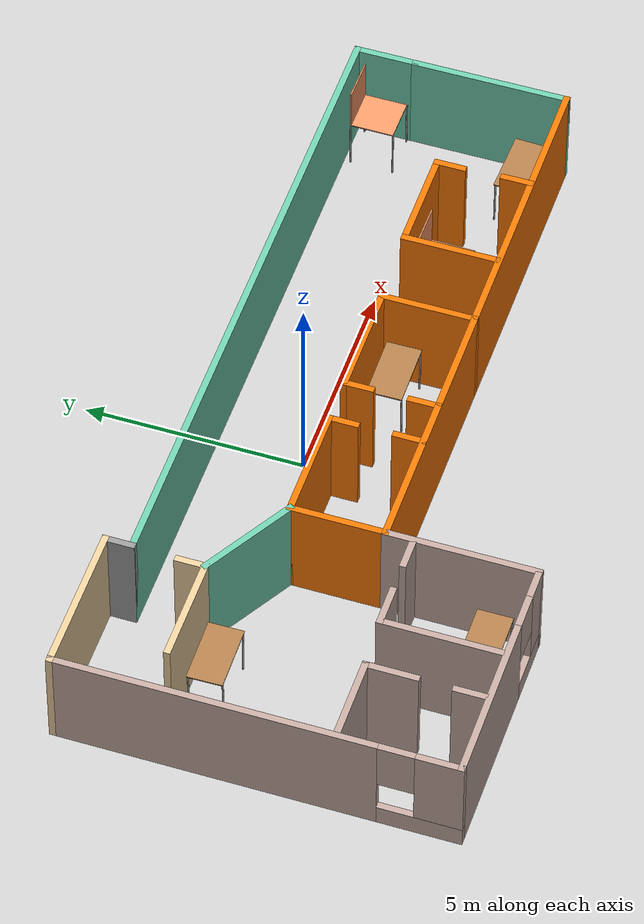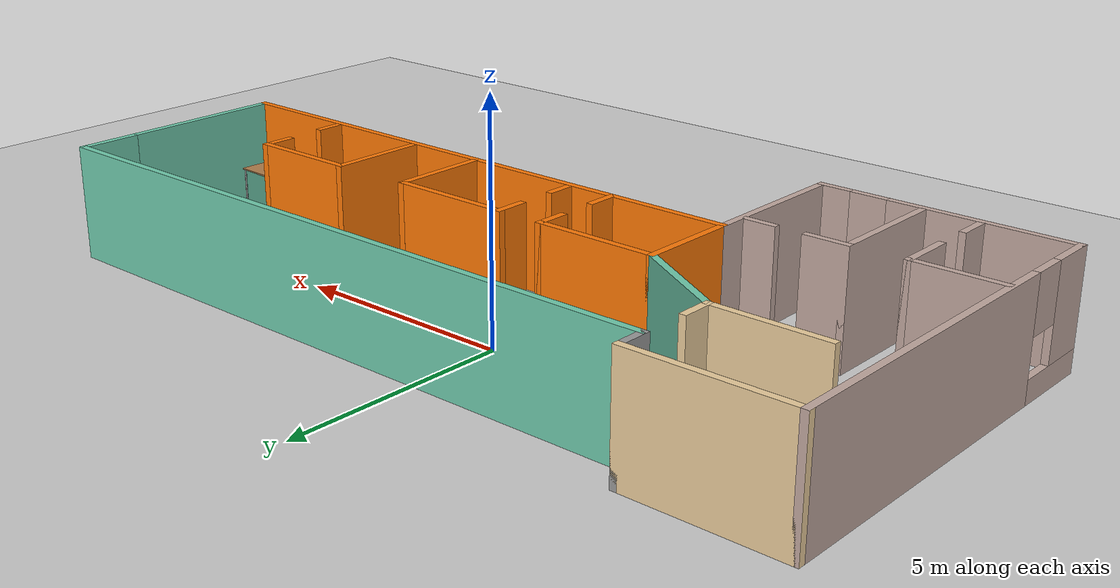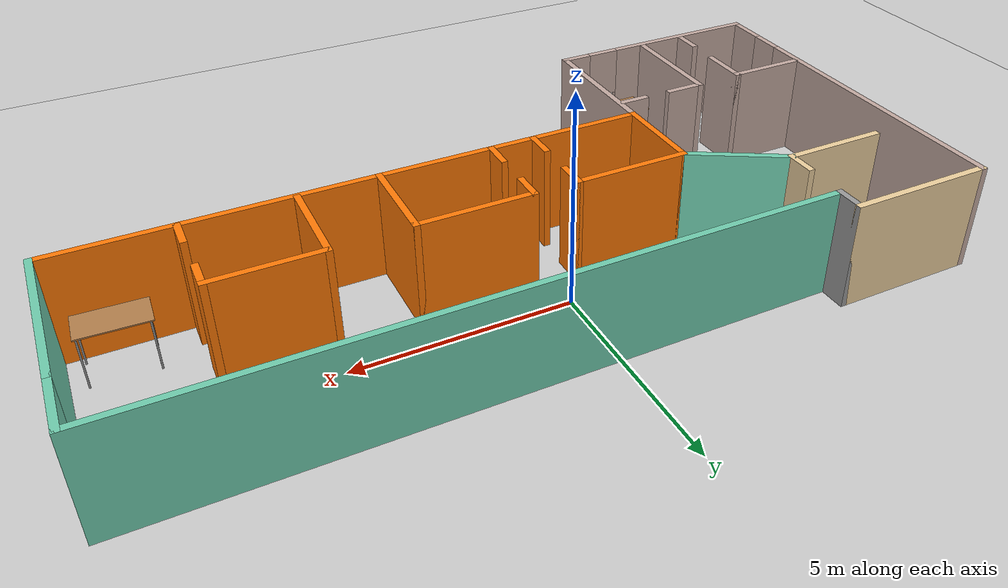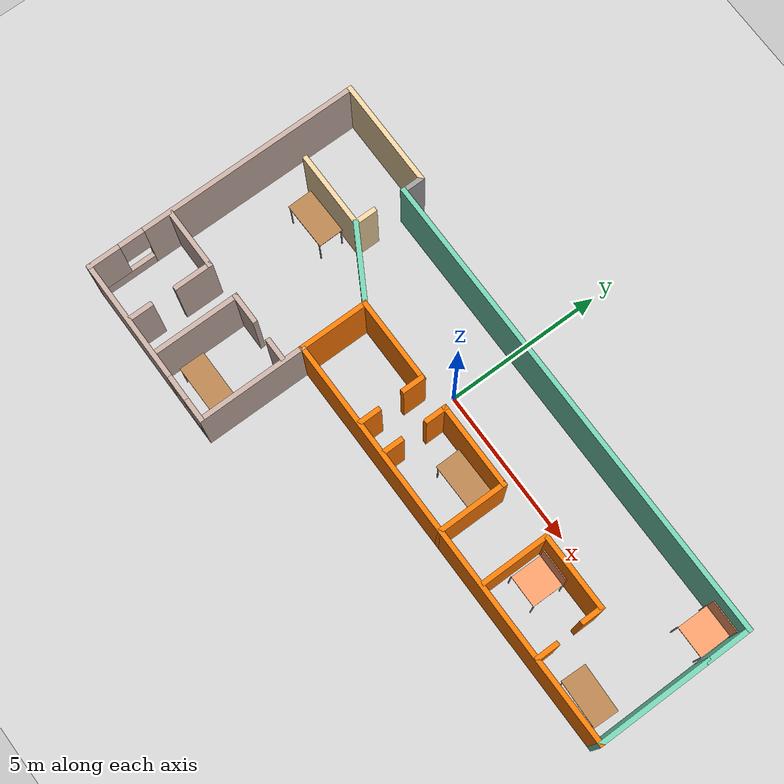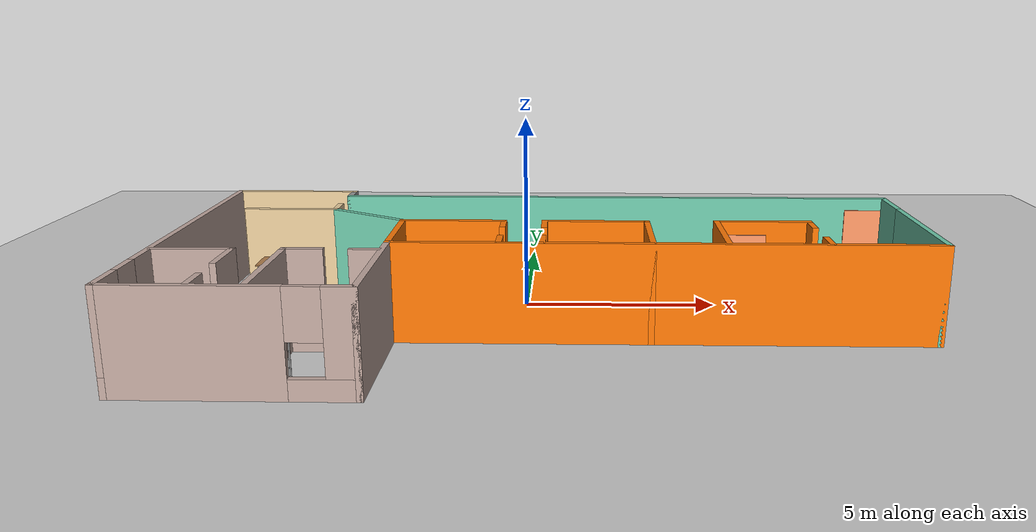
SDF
<sdf version="1.7">
 <world name="default">
  <light name="sun" type="directional">
   <pose>0 0 10 0 -0 0</pose>
   <diffuse>0.8 0.8 0.8 1</diffuse>
   <specular>0.2 0.2 0.2 1</specular>
   <attenuation>
    <range>1000</range>
    <constant>0.9</constant>
    <linear>0.01</linear>
    <quadratic>0.001</quadratic>
   </attenuation>
   <direction>-0.5 0.1 -0.9</direction>
   <spot><inner_angle>0</inner_angle><outer_angle>0</outer_angle><falloff>0</falloff></spot>
  </light>
  <model name="ground_plane">
   <static>1</static>
   <link name="link">
    <collision name="collision">
     <geometry><plane><normal>0 0 1</normal><size>100 100</size></plane></geometry>
     <surface>
      <contact><collide_bitmask>65535</collide_bitmask></contact>
      <friction><ode><mu>100</mu><mu2>50</mu2></ode></friction>
     </surface>
    </collision>
    <visual name="visual">
     <cast_shadows>0</cast_shadows>
     <geometry><plane><normal>0 0 1</normal><size>100 100</size></plane></geometry>
     <material>
      <script><uri>file://media/materials/scripts/gazebo.material</uri><name>Gazebo/Grey</name></script>
     </material>
    </visual>
   </link>
  </model>
  <gravity>0 0 -9.8</gravity>
  <magnetic_field>6e-06 2.3e-05 -4.2e-05</magnetic_field>
  <atmosphere type="adiabatic"/>
  <physics type="ode">
   <max_step_size>0.001</max_step_size>
   <real_time_factor>1</real_time_factor>
   <real_time_update_rate>1000</real_time_update_rate>
  </physics>
  <scene><ambient>0.4 0.4 0.4 1</ambient><background>0.7 0.7 0.7 1</background><shadows>1</shadows></scene>
  <spherical_coordinates>
   <surface_model>EARTH_WGS84</surface_model>
   <latitude_deg>0</latitude_deg>
   <longitude_deg>0</longitude_deg>
   <elevation>0</elevation>
   <heading_deg>0</heading_deg>
  </spherical_coordinates>
  <model name="Building">
   <pose>0.744331 -1.77373 0 0 -0 0</pose>
   <link name="Wall_101">
    <collision name="Wall_101_Collision">
     <geometry><box><size>3.5 0.15 2.5</size></box></geometry>
     <pose>0 0 1.25 0 -0 0</pose>
    </collision>
    <visual name="Wall_101_Visual">
     <pose>0 0 1.25 0 -0 0</pose>
     <geometry><box><size>3.5 0.15 2.5</size></box></geometry>
     <material>
      <script><uri>file://media/materials/scripts/gazebo.material</uri><name>Gazebo/Grey</name></script>
      <ambient>0.921569 0.807843 0.615686 1</ambient>
     </material>
     <meta><layer>0</layer></meta>
    </visual>
    <pose>-7.55 4.425 0 0 -0 0</pose>
   </link>
   <link name="Wall_102">
    <collision name="Wall_102_Collision">
     <geometry><box><size>0.75 0.15 2.5</size></box></geometry>
     <pose>0 0 1.25 0 -0 0</pose>
    </collision>
    <visual name="Wall_102_Visual">
     <pose>0 0 1.25 0 -0 0</pose>
     <geometry><box><size>0.75 0.15 2.5</size></box></geometry>
     <material>
      <script><uri>file://media/materials/scripts/gazebo.material</uri><name>Gazebo/Grey</name></script>
      <ambient>1 1 1 1</ambient>
     </material>
     <meta><layer>0</layer></meta>
    </visual>
    <pose>-5.875 4.125 0 0 -0 -1.5708</pose>
   </link>
   <link name="Wall_109">
    <collision name="Wall_109_Collision">
     <geometry><box><size>2.5 0.15 2.5</size></box></geometry>
     <pose>0 0 1.25 0 -0 0</pose>
    </collision>
    <visual name="Wall_109_Visual">
     <pose>0 0 1.25 0 -0 0</pose>
     <geometry><box><size>2.5 0.15 2.5</size></box></geometry>
     <material>
      <script><uri>file://media/materials/scripts/gazebo.material</uri><name>Gazebo/Grey</name></script>
      <ambient>0.435294 0.796078 0.67451 1</ambient>
     </material>
     <meta><layer>0</layer></meta>
    </visual>
    <pose>-4.89258 1.6125 0 0 -0 2.61799</pose>
   </link>
   <link name="Wall_110">
    <collision name="Wall_110_Collision">
     <geometry><box><size>2.5 0.15 2.5</size></box></geometry>
     <pose>0 0 1.25 0 -0 0</pose>
    </collision>
    <visual name="Wall_110_Visual">
     <pose>0 0 1.25 0 -0 0</pose>
     <geometry><box><size>2.5 0.15 2.5</size></box></geometry>
     <material>
      <script><uri>file://media/materials/scripts/gazebo.material</uri><name>Gazebo/Grey</name></script>
      <ambient>0.921569 0.807843 0.615686 1</ambient>
     </material>
     <meta><layer>0</layer></meta>
    </visual>
    <pose>-7.08516 2.2 0 0 -0 3.14159</pose>
   </link>
   <link name="Wall_112">
    <collision name="Wall_112_Collision">
     <geometry><box><size>0.75 0.15 2.5</size></box></geometry>
     <pose>0 0 1.25 0 -0 0</pose>
    </collision>
    <visual name="Wall_112_Visual">
     <pose>0 0 1.25 0 -0 0</pose>
     <geometry><box><size>0.75 0.15 2.5</size></box></geometry>
     <material>
      <script><uri>file://media/materials/scripts/gazebo.material</uri><name>Gazebo/Grey</name></script>
      <ambient>0.921569 0.807843 0.615686 1</ambient>
     </material>
     <meta><layer>0</layer></meta>
    </visual>
    <pose>-5.91016 2.5 0 0 -0 1.5708</pose>
   </link>
   <link name="Wall_125">
    <collision name="Wall_125_Collision">
     <geometry><box><size>15.25 0.15 2.5</size></box></geometry>
     <pose>0 0 1.25 0 -0 0</pose>
    </collision>
    <visual name="Wall_125_Visual">
     <pose>0 0 1.25 0 -0 0</pose>
     <geometry><box><size>15.25 0.15 2.5</size></box></geometry>
     <material>
      <script><uri>file://media/materials/scripts/gazebo.material</uri><name>Gazebo/Grey</name></script>
      <ambient>0.435294 0.796078 0.67451 1</ambient>
     </material>
     <meta><layer>0</layer></meta>
    </visual>
    <pose>1.675 3.825 0 0 -0 0</pose>
   </link>
   <link name="Wall_126">
    <collision name="Wall_126_Collision">
     <geometry><box><size>1.51891 0.15 2.5</size></box></geometry>
     <pose>0 0 1.25 0 -0 0</pose>
    </collision>
    <visual name="Wall_126_Visual">
     <pose>0 0 1.25 0 -0 0</pose>
     <geometry><box><size>1.51891 0.15 2.5</size></box></geometry>
     <material>
      <script><uri>file://media/materials/scripts/gazebo.material</uri><name>Gazebo/Grey</name></script>
      <ambient>0.435294 0.796078 0.67451 1</ambient>
     </material>
     <meta><layer>0</layer></meta>
    </visual>
    <pose>9.225 3.14054 0 0 -0 -1.5708</pose>
   </link>
   <link name="Wall_139">
    <collision name="Wall_139_Collision">
     <geometry><box><size>2.75 0.15 2.5</size></box></geometry>
     <pose>0 0 1.25 0 -0 0</pose>
    </collision>
    <visual name="Wall_139_Visual">
     <pose>0 0 1.25 0 -0 0</pose>
     <geometry><box><size>2.75 0.15 2.5</size></box></geometry>
     <material>
      <script><uri>file://media/materials/scripts/gazebo.material</uri><name>Gazebo/Grey</name></script>
      <ambient>0.760784 0.662745 0.627451 1</ambient>
     </material>
     <meta><layer>0</layer></meta>
    </visual>
    <pose>-6.14157 -2.98957 0 0 -0 1.5708</pose>
   </link>
   <link name="Wall_143">
    <collision name="Wall_143_Collision">
     <geometry><box><size>0.75 0.15 2.5</size></box></geometry>
     <pose>0 0 1.25 0 -0 0</pose>
    </collision>
    <visual name="Wall_143_Visual">
     <pose>0 0 1.25 0 -0 0</pose>
     <geometry><box><size>0.75 0.15 2.5</size></box></geometry>
     <material>
      <script><uri>file://media/materials/scripts/gazebo.material</uri><name>Gazebo/Grey</name></script>
      <ambient>0.760784 0.662745 0.627451 1</ambient>
     </material>
     <meta><layer>0</layer></meta>
    </visual>
    <pose>-4.27222 -1.69272 0 0 -0 3.14159</pose>
   </link>
   <link name="Wall_146">
    <collision name="Wall_146_Collision">
     <geometry><box><size>2 0.15 2.5</size></box></geometry>
     <pose>0 0 1.25 0 -0 0</pose>
    </collision>
    <visual name="Wall_146_Visual">
     <pose>0 0 1.25 0 -0 0</pose>
     <geometry><box><size>2 0.15 2.5</size></box></geometry>
     <material>
      <script><uri>file://media/materials/scripts/gazebo.material</uri><name>Gazebo/Grey</name></script>
      <ambient>0.760784 0.662745 0.627451 1</ambient>
     </material>
     <meta><layer>0</layer></meta>
    </visual>
    <pose>-8.24301 -1.74784 0 0 -0 0</pose>
   </link>
   <link name="Wall_147">
    <collision name="Wall_147_Collision">
     <geometry><box><size>1.25 0.15 2.5</size></box></geometry>
     <pose>0 0 1.25 0 -0 0</pose>
    </collision>
    <visual name="Wall_147_Visual">
     <pose>0 0 1.25 0 -0 0</pose>
     <geometry><box><size>1.25 0.15 2.5</size></box></geometry>
     <material>
      <script><uri>file://media/materials/scripts/gazebo.material</uri><name>Gazebo/Grey</name></script>
      <ambient>0.760784 0.662745 0.627451 1</ambient>
     </material>
     <meta><layer>0</layer></meta>
    </visual>
    <pose>-7.31801 -2.29784 0 0 -0 -1.5708</pose>
   </link>
   <link name="Wall_150">
    <collision name="Wall_150_Collision">
     <geometry><box><size>0.75 0.15 2.5</size></box></geometry>
     <pose>0 0 1.25 0 -0 0</pose>
    </collision>
    <visual name="Wall_150_Visual">
     <pose>0 0 1.25 0 -0 0</pose>
     <geometry><box><size>0.75 0.15 2.5</size></box></geometry>
     <material>
      <script><uri>file://media/materials/scripts/gazebo.material</uri><name>Gazebo/Grey</name></script>
      <ambient>0.760784 0.662745 0.627451 1</ambient>
     </material>
     <meta><layer>0</layer></meta>
    </visual>
    <pose>-7.33501 -4.0068 0 0 -0 -1.5708</pose>
   </link>
   <link name="Wall_152">
    <collision name="Wall_152_Collision">
     <geometry><box><size>1 0.15 2.5</size></box></geometry>
     <pose>0 0 1.25 0 -0 0</pose>
    </collision>
    <visual name="Wall_152_Visual">
     <pose>0 0 1.25 0 -0 0</pose>
     <geometry><box><size>1 0.15 2.5</size></box></geometry>
     <material>
      <script><uri>file://media/materials/scripts/gazebo.material</uri><name>Gazebo/Grey</name></script>
      <ambient>0.760784 0.662745 0.627451 1</ambient>
     </material>
     <meta><layer>0</layer></meta>
    </visual>
    <pose>-5.71657 -1.68957 0 0 -0 0</pose>
   </link>
   <link name="Wall_21">
    <pose>-6.55 -4.425 0 0 -0 0</pose>
    <visual name="Wall_21_Visual_0">
     <pose>-0.779518 0 1.25 0 -0 0</pose>
     <geometry><box><size>3.94096 0.15 2.5</size></box></geometry>
     <material>
      <script><uri>file://media/materials/scripts/gazebo.material</uri><name>Gazebo/Grey</name></script>
      <ambient>0.760784 0.662745 0.627451 1</ambient>
     </material>
     <meta><layer>0</layer></meta>
    </visual>
    <collision name="Wall_21_Collision_0">
     <geometry><box><size>3.94096 0.15 2.5</size></box></geometry>
     <pose>-0.779518 0 1.25 0 -0 0</pose>
    </collision>
    <visual name="Wall_21_Visual_1">
     <pose>1.97048 0 0.25 0 -0 0</pose>
     <geometry><box><size>1.55904 0.15 0.5</size></box></geometry>
     <material>
      <script><uri>file://media/materials/scripts/gazebo.material</uri><name>Gazebo/Grey</name></script>
      <ambient>0.760784 0.662745 0.627451 1</ambient>
     </material>
     <meta><layer>0</layer></meta>
    </visual>
    <collision name="Wall_21_Collision_1">
     <geometry><box><size>1.55904 0.15 0.5</size></box></geometry>
     <pose>1.97048 0 0.25 0 -0 0</pose>
    </collision>
    <visual name="Wall_21_Visual_2">
     <pose>2.37048 0 1.5 0 -0 0</pose>
     <geometry><box><size>0.759036 0.15 2</size></box></geometry>
     <material>
      <script><uri>file://media/materials/scripts/gazebo.material</uri><name>Gazebo/Grey</name></script>
      <ambient>0.760784 0.662745 0.627451 1</ambient>
     </material>
     <meta><layer>0</layer></meta>
    </visual>
    <collision name="Wall_21_Collision_2">
     <geometry><box><size>0.759036 0.15 2</size></box></geometry>
     <pose>2.37048 0 1.5 0 -0 0</pose>
    </collision>
    <visual name="Wall_21_Visual_3">
     <pose>1.59096 0 1.9 0 -0 0</pose>
     <geometry><box><size>0.8 0.15 1.2</size></box></geometry>
     <material>
      <script><uri>file://media/materials/scripts/gazebo.material</uri><name>Gazebo/Grey</name></script>
      <ambient>0.760784 0.662745 0.627451 1</ambient>
     </material>
     <meta><layer>0</layer></meta>
    </visual>
    <collision name="Wall_21_Collision_3">
     <geometry><box><size>0.8 0.15 1.2</size></box></geometry>
     <pose>1.59096 0 1.9 0 -0 0</pose>
    </collision>
   </link>
   <link name="Wall_23">
    <collision name="Wall_23_Collision">
     <geometry><box><size>3.5 0.15 2.5</size></box></geometry>
     <pose>0 0 1.25 0 -0 0</pose>
    </collision>
    <visual name="Wall_23_Visual">
     <pose>0 0 1.25 0 -0 0</pose>
     <geometry><box><size>3.5 0.15 2.5</size></box></geometry>
     <material>
      <script><uri>file://media/materials/scripts/gazebo.material</uri><name>Gazebo/Grey</name></script>
      <ambient>0.760784 0.662745 0.627451 1</ambient>
     </material>
     <meta><layer>0</layer></meta>
    </visual>
    <pose>-3.875 -2.75 0 0 -0 1.5708</pose>
   </link>
   <link name="Wall_24">
    <collision name="Wall_24_Collision">
     <geometry><box><size>13.25 0.15 2.5</size></box></geometry>
     <pose>0 0 1.25 0 -0 0</pose>
    </collision>
    <visual name="Wall_24_Visual">
     <pose>0 0 1.25 0 -0 0</pose>
     <geometry><box><size>13.25 0.15 2.5</size></box></geometry>
     <material>
      <script><uri>file://media/materials/scripts/gazebo.material</uri><name>Gazebo/Grey</name></script>
      <ambient>0.996078 0.47451 0.0196078 1</ambient>
     </material>
     <meta><layer>0</layer></meta>
    </visual>
    <pose>2.675 -1.075 0 0 -0 0</pose>
   </link>
   <link name="Wall_25">
    <collision name="Wall_25_Collision">
     <geometry><box><size>3.68109 0.15 2.5</size></box></geometry>
     <pose>0 0 1.25 0 -0 0</pose>
    </collision>
    <visual name="Wall_25_Visual">
     <pose>0 0 1.25 0 -0 0</pose>
     <geometry><box><size>3.68109 0.15 2.5</size></box></geometry>
     <material>
      <script><uri>file://media/materials/scripts/gazebo.material</uri><name>Gazebo/Grey</name></script>
      <ambient>0.435294 0.796078 0.67451 1</ambient>
     </material>
     <meta><layer>0</layer></meta>
    </visual>
    <pose>9.225 0.690545 0 0 -0 1.5708</pose>
   </link>
   <link name="Wall_38">
    <collision name="Wall_38_Collision">
     <geometry><box><size>2.25 0.15 2.5</size></box></geometry>
     <pose>0 0 1.25 0 -0 0</pose>
    </collision>
    <visual name="Wall_38_Visual">
     <pose>0 0 1.25 0 -0 0</pose>
     <geometry><box><size>2.25 0.15 2.5</size></box></geometry>
     <material>
      <script><uri>file://media/materials/scripts/gazebo.material</uri><name>Gazebo/Grey</name></script>
      <ambient>0.996078 0.47451 0.0196078 1</ambient>
     </material>
     <meta><layer>0</layer></meta>
    </visual>
    <pose>-3.875 -0.025 0 0 -0 1.5708</pose>
   </link>
   <link name="Wall_39">
    <collision name="Wall_39_Collision">
     <geometry><box><size>2.75 0.15 2.5</size></box></geometry>
     <pose>0 0 1.25 0 -0 0</pose>
    </collision>
    <visual name="Wall_39_Visual">
     <pose>0 0 1.25 0 -0 0</pose>
     <geometry><box><size>2.75 0.15 2.5</size></box></geometry>
     <material>
      <script><uri>file://media/materials/scripts/gazebo.material</uri><name>Gazebo/Grey</name></script>
      <ambient>0.996078 0.47451 0.0196078 1</ambient>
     </material>
     <meta><layer>0</layer></meta>
    </visual>
    <pose>-2.575 1.025 0 0 -0 0</pose>
   </link>
   <link name="Wall_4">
    <pose>-9.225 -0 0 0 -0 -1.5708</pose>
    <visual name="Wall_4_Visual_0">
     <pose>-0.927991 0 1.25 0 -0 0</pose>
     <geometry><box><size>7.14402 0.15 2.5</size></box></geometry>
     <material>
      <script><uri>file://media/materials/scripts/gazebo.material</uri><name>Gazebo/Grey</name></script>
      <ambient>0.760784 0.662745 0.627451 1</ambient>
     </material>
     <meta><layer>0</layer></meta>
    </visual>
    <collision name="Wall_4_Collision_0">
     <geometry><box><size>7.14402 0.15 2.5</size></box></geometry>
     <pose>-0.927991 0 1.25 0 -0 0</pose>
    </collision>
    <visual name="Wall_4_Visual_1">
     <pose>3.57201 0 0.25 0 -0 0</pose>
     <geometry><box><size>1.85598 0.15 0.5</size></box></geometry>
     <material>
      <script><uri>file://media/materials/scripts/gazebo.material</uri><name>Gazebo/Grey</name></script>
      <ambient>0.760784 0.662745 0.627451 1</ambient>
     </material>
     <meta><layer>0</layer></meta>
    </visual>
    <collision name="Wall_4_Collision_1">
     <geometry><box><size>1.85598 0.15 0.5</size></box></geometry>
     <pose>3.57201 0 0.25 0 -0 0</pose>
    </collision>
    <visual name="Wall_4_Visual_2">
     <pose>3.97201 0 1.5 0 -0 0</pose>
     <geometry><box><size>1.05598 0.15 2</size></box></geometry>
     <material>
      <script><uri>file://media/materials/scripts/gazebo.material</uri><name>Gazebo/Grey</name></script>
      <ambient>0.760784 0.662745 0.627451 1</ambient>
     </material>
     <meta><layer>0</layer></meta>
    </visual>
    <collision name="Wall_4_Collision_2">
     <geometry><box><size>1.05598 0.15 2</size></box></geometry>
     <pose>3.97201 0 1.5 0 -0 0</pose>
    </collision>
    <visual name="Wall_4_Visual_3">
     <pose>3.04402 0 1.9 0 -0 0</pose>
     <geometry><box><size>0.8 0.15 1.2</size></box></geometry>
     <material>
      <script><uri>file://media/materials/scripts/gazebo.material</uri><name>Gazebo/Grey</name></script>
      <ambient>0.760784 0.662745 0.627451 1</ambient>
     </material>
     <meta><layer>0</layer></meta>
    </visual>
    <collision name="Wall_4_Collision_3">
     <geometry><box><size>0.8 0.15 1.2</size></box></geometry>
     <pose>3.04402 0 1.9 0 -0 0</pose>
    </collision>
   </link>
   <link name="Wall_40">
    <collision name="Wall_40_Collision">
     <geometry><box><size>0.75 0.15 2.5</size></box></geometry>
     <pose>0 0 1.25 0 -0 0</pose>
    </collision>
    <visual name="Wall_40_Visual">
     <pose>0 0 1.25 0 -0 0</pose>
     <geometry><box><size>0.75 0.15 2.5</size></box></geometry>
     <material>
      <script><uri>file://media/materials/scripts/gazebo.material</uri><name>Gazebo/Grey</name></script>
      <ambient>0.996078 0.47451 0.0196078 1</ambient>
     </material>
     <meta><layer>0</layer></meta>
    </visual>
    <pose>-1.275 0.725 0 0 -0 -1.5708</pose>
   </link>
   <link name="Wall_58">
    <collision name="Wall_58_Collision">
     <geometry><box><size>0.75 0.15 2.5</size></box></geometry>
     <pose>0 0 1.25 0 -0 0</pose>
    </collision>
    <visual name="Wall_58_Visual">
     <pose>0 0 1.25 0 -0 0</pose>
     <geometry><box><size>0.75 0.15 2.5</size></box></geometry>
     <material>
      <script><uri>file://media/materials/scripts/gazebo.material</uri><name>Gazebo/Grey</name></script>
      <ambient>0.996078 0.47451 0.0196078 1</ambient>
     </material>
     <meta><layer>0</layer></meta>
    </visual>
    <pose>-0.23631 0.725 0 0 -0 -1.5708</pose>
   </link>
   <link name="Wall_70">
    <collision name="Wall_70_Collision">
     <geometry><box><size>0.75 0.15 2.5</size></box></geometry>
     <pose>0 0 1.25 0 -0 0</pose>
    </collision>
    <visual name="Wall_70_Visual">
     <pose>0 0 1.25 0 -0 0</pose>
     <geometry><box><size>0.75 0.15 2.5</size></box></geometry>
     <material>
      <script><uri>file://media/materials/scripts/gazebo.material</uri><name>Gazebo/Grey</name></script>
      <ambient>0.996078 0.47451 0.0196078 1</ambient>
     </material>
     <meta><layer>0</layer></meta>
    </visual>
    <pose>-1.2639 -0.761486 0 0 -0 1.5708</pose>
   </link>
   <link name="Wall_72">
    <collision name="Wall_72_Collision">
     <geometry><box><size>0.75 0.15 2.5</size></box></geometry>
     <pose>0 0 1.25 0 -0 0</pose>
    </collision>
    <visual name="Wall_72_Visual">
     <pose>0 0 1.25 0 -0 0</pose>
     <geometry><box><size>0.75 0.15 2.5</size></box></geometry>
     <material>
      <script><uri>file://media/materials/scripts/gazebo.material</uri><name>Gazebo/Grey</name></script>
      <ambient>0.996078 0.47451 0.0196078 1</ambient>
     </material>
     <meta><layer>0</layer></meta>
    </visual>
    <pose>-0.23182 -0.762321 0 0 -0 -1.5708</pose>
   </link>
   <link name="Wall_74">
    <collision name="Wall_74_Collision">
     <geometry><box><size>2.75 0.15 2.5</size></box></geometry>
     <pose>0 0 1.25 0 -0 0</pose>
    </collision>
    <visual name="Wall_74_Visual">
     <pose>0 0 1.25 0 -0 0</pose>
     <geometry><box><size>2.75 0.15 2.5</size></box></geometry>
     <material>
      <script><uri>file://media/materials/scripts/gazebo.material</uri><name>Gazebo/Grey</name></script>
      <ambient>0.996078 0.47451 0.0196078 1</ambient>
     </material>
     <meta><layer>0</layer></meta>
    </visual>
    <pose>1.06369 1.025 0 0 -0 0</pose>
   </link>
   <link name="Wall_75">
    <collision name="Wall_75_Collision">
     <geometry><box><size>2.25 0.15 2.5</size></box></geometry>
     <pose>0 0 1.25 0 -0 0</pose>
    </collision>
    <visual name="Wall_75_Visual">
     <pose>0 0 1.25 0 -0 0</pose>
     <geometry><box><size>2.25 0.15 2.5</size></box></geometry>
     <material>
      <script><uri>file://media/materials/scripts/gazebo.material</uri><name>Gazebo/Grey</name></script>
      <ambient>0.996078 0.47451 0.0196078 1</ambient>
     </material>
     <meta><layer>0</layer></meta>
    </visual>
    <pose>2.36369 -0.025 0 0 -0 -1.5708</pose>
   </link>
   <link name="Wall_83">
    <collision name="Wall_83_Collision">
     <geometry><box><size>2.25 0.15 2.5</size></box></geometry>
     <pose>0 0 1.25 0 -0 0</pose>
    </collision>
    <visual name="Wall_83_Visual">
     <pose>0 0 1.25 0 -0 0</pose>
     <geometry><box><size>2.25 0.15 2.5</size></box></geometry>
     <material>
      <script><uri>file://media/materials/scripts/gazebo.material</uri><name>Gazebo/Grey</name></script>
      <ambient>0.996078 0.47451 0.0196078 1</ambient>
     </material>
     <meta><layer>0</layer></meta>
    </visual>
    <pose>4.14244 0.031114 0 0 -0 1.5708</pose>
   </link>
   <link name="Wall_84">
    <collision name="Wall_84_Collision">
     <geometry><box><size>2.5 0.15 2.5</size></box></geometry>
     <pose>0 0 1.25 0 -0 0</pose>
    </collision>
    <visual name="Wall_84_Visual">
     <pose>0 0 1.25 0 -0 0</pose>
     <geometry><box><size>2.5 0.15 2.5</size></box></geometry>
     <material>
      <script><uri>file://media/materials/scripts/gazebo.material</uri><name>Gazebo/Grey</name></script>
      <ambient>0.996078 0.47451 0.0196078 1</ambient>
     </material>
     <meta><layer>0</layer></meta>
    </visual>
    <pose>5.31744 1.08111 0 0 -0 0</pose>
   </link>
   <link name="Wall_85">
    <collision name="Wall_85_Collision">
     <geometry><box><size>0.75 0.15 2.5</size></box></geometry>
     <pose>0 0 1.25 0 -0 0</pose>
    </collision>
    <visual name="Wall_85_Visual">
     <pose>0 0 1.25 0 -0 0</pose>
     <geometry><box><size>0.75 0.15 2.5</size></box></geometry>
     <material>
      <script><uri>file://media/materials/scripts/gazebo.material</uri><name>Gazebo/Grey</name></script>
      <ambient>0.996078 0.47451 0.0196078 1</ambient>
     </material>
     <meta><layer>0</layer></meta>
    </visual>
    <pose>6.49244 0.781114 0 0 -0 -1.5708</pose>
   </link>
   <link name="Wall_88">
    <collision name="Wall_88_Collision">
     <geometry><box><size>0.75 0.15 2.5</size></box></geometry>
     <pose>0 0 1.25 0 -0 0</pose>
    </collision>
    <visual name="Wall_88_Visual">
     <pose>0 0 1.25 0 -0 0</pose>
     <geometry><box><size>0.75 0.15 2.5</size></box></geometry>
     <material>
      <script><uri>file://media/materials/scripts/gazebo.material</uri><name>Gazebo/Grey</name></script>
      <ambient>0.996078 0.47451 0.0196078 1</ambient>
     </material>
     <meta><layer>0</layer></meta>
    </visual>
    <pose>6.53567 -0.750584 0 0 -0 1.5708</pose>
   </link>
   <static>1</static>
  </model>
  <model name="Regular_Table">
   <link name="link_0">
    <inertial>
     <mass>1</mass>
     <inertia>
      <ixx>0.166667</ixx>
      <ixy>0</ixy>
      <ixz>0</ixz>
      <iyy>0.166667</iyy>
      <iyz>0</iyz>
      <izz>0.166667</izz>
     </inertia>
    </inertial>
    <pose>-0 0 1.2 0 -0 0</pose>
    <visual name="visual">
     <geometry><box><size>1.5 0.8 0.03</size></box></geometry>
     <material>
      <lighting>1</lighting>
      <script><uri>file://media/materials/scripts/gazebo.material</uri><name>Gazebo/Wood</name></script>
      <shader type="pixel"><normal_map>__default__</normal_map></shader>
      <ambient>0.3 0.3 0.3 1</ambient>
      <diffuse>0.7 0.7 0.7 1</diffuse>
      <specular>0.01 0.01 0.01 1</specular>
      <emissive>0 0 0 1</emissive>
     </material>
    </visual>
    <collision name="collision">
     <geometry><box><size>1.5 0.8 0.03</size></box></geometry>
     <surface>
      <friction>
       <ode><mu>1</mu><mu2>1</mu2><fdir1>0 0 0</fdir1><slip1>0</slip1><slip2>0</slip2></ode>
       <torsional>
        <coefficient>1</coefficient>
        <patch_radius>0</patch_radius>
        <surface_radius>0</surface_radius>
        <use_patch_radius>1</use_patch_radius>
        <ode><slip>0</slip></ode>
       </torsional>
      </friction>
      <bounce><restitution_coefficient>0</restitution_coefficient><threshold>1e+06</threshold></bounce>
      <contact>
       <collide_without_contact>0</collide_without_contact>
       <collide_without_contact_bitmask>1</collide_without_contact_bitmask>
       <collide_bitmask>1</collide_bitmask>
       <ode>
        <soft_cfm>0</soft_cfm>
        <soft_erp>0.2</soft_erp>
        <kp>1e+13</kp>
        <kd>1</kd>
        <max_vel>0.01</max_vel>
        <min_depth>0</min_depth>
       </ode>
       <bullet>
        <split_impulse>1</split_impulse>
        <split_impulse_penetration_threshold>-0.01</split_impulse_penetration_threshold>
        <soft_cfm>0</soft_cfm>
        <soft_erp>0.2</soft_erp>
        <kp>1e+13</kp>
        <kd>1</kd>
       </bullet>
      </contact>
     </surface>
    </collision>
   </link>
   <link name="link_3">
    <inertial>
     <mass>1</mass>
     <inertia><ixx>0.145833</ixx><ixy>0</ixy><ixz>0</ixz><iyy>0.145833</iyy><iyz>0</iyz><izz>0.125</izz></inertia>
    </inertial>
    <pose>0.68 0.38 0.6 0 -0 0</pose>
    <visual name="visual">
     <geometry><cylinder><radius>0.02</radius><length>1.2</length></cylinder></geometry>
     <material>
      <lighting>1</lighting>
      <script><uri>file://media/materials/scripts/gazebo.material</uri><name>Gazebo/Grey</name></script>
      <shader type="pixel"><normal_map>__default__</normal_map></shader>
      <ambient>0.3 0.3 0.3 1</ambient>
      <diffuse>0.7 0.7 0.7 1</diffuse>
      <specular>0.01 0.01 0.01 1</specular>
      <emissive>0 0 0 1</emissive>
     </material>
    </visual>
    <collision name="collision">
     <geometry><cylinder><radius>0.02</radius><length>1.2</length></cylinder></geometry>
     <surface>
      <friction>
       <ode><mu>1</mu><mu2>1</mu2><fdir1>0 0 0</fdir1><slip1>0</slip1><slip2>0</slip2></ode>
       <torsional>
        <coefficient>1</coefficient>
        <patch_radius>0</patch_radius>
        <surface_radius>0</surface_radius>
        <use_patch_radius>1</use_patch_radius>
        <ode><slip>0</slip></ode>
       </torsional>
      </friction>
      <bounce><restitution_coefficient>0</restitution_coefficient><threshold>1e+06</threshold></bounce>
      <contact>
       <collide_without_contact>0</collide_without_contact>
       <collide_without_contact_bitmask>1</collide_without_contact_bitmask>
       <collide_bitmask>1</collide_bitmask>
       <ode>
        <soft_cfm>0</soft_cfm>
        <soft_erp>0.2</soft_erp>
        <kp>1e+13</kp>
        <kd>1</kd>
        <max_vel>0.01</max_vel>
        <min_depth>0</min_depth>
       </ode>
       <bullet>
        <split_impulse>1</split_impulse>
        <split_impulse_penetration_threshold>-0.01</split_impulse_penetration_threshold>
        <soft_cfm>0</soft_cfm>
        <soft_erp>0.2</soft_erp>
        <kp>1e+13</kp>
        <kd>1</kd>
       </bullet>
      </contact>
     </surface>
    </collision>
   </link>
   <link name="link_3_clone">
    <inertial>
     <mass>1</mass>
     <inertia><ixx>0.145833</ixx><ixy>0</ixy><ixz>0</ixz><iyy>0.145833</iyy><iyz>0</iyz><izz>0.125</izz></inertia>
    </inertial>
    <pose>0.68 -0.38 0.6 0 -0 0</pose>
    <visual name="visual">
     <geometry><cylinder><radius>0.02</radius><length>1.2</length></cylinder></geometry>
     <material>
      <lighting>1</lighting>
      <script><uri>file://media/materials/scripts/gazebo.material</uri><name>Gazebo/Grey</name></script>
      <shader type="pixel"><normal_map>__default__</normal_map></shader>
      <ambient>0.3 0.3 0.3 1</ambient>
      <diffuse>0.7 0.7 0.7 1</diffuse>
      <specular>0.01 0.01 0.01 1</specular>
      <emissive>0 0 0 1</emissive>
     </material>
    </visual>
    <collision name="collision">
     <geometry><cylinder><radius>0.02</radius><length>1.2</length></cylinder></geometry>
     <surface>
      <friction>
       <ode><mu>1</mu><mu2>1</mu2><fdir1>0 0 0</fdir1><slip1>0</slip1><slip2>0</slip2></ode>
       <torsional>
        <coefficient>1</coefficient>
        <patch_radius>0</patch_radius>
        <surface_radius>0</surface_radius>
        <use_patch_radius>1</use_patch_radius>
        <ode><slip>0</slip></ode>
       </torsional>
      </friction>
      <bounce><restitution_coefficient>0</restitution_coefficient><threshold>1e+06</threshold></bounce>
      <contact>
       <collide_without_contact>0</collide_without_contact>
       <collide_without_contact_bitmask>1</collide_without_contact_bitmask>
       <collide_bitmask>1</collide_bitmask>
       <ode>
        <soft_cfm>0</soft_cfm>
        <soft_erp>0.2</soft_erp>
        <kp>1e+13</kp>
        <kd>1</kd>
        <max_vel>0.01</max_vel>
        <min_depth>0</min_depth>
       </ode>
       <bullet>
        <split_impulse>1</split_impulse>
        <split_impulse_penetration_threshold>-0.01</split_impulse_penetration_threshold>
        <soft_cfm>0</soft_cfm>
        <soft_erp>0.2</soft_erp>
        <kp>1e+13</kp>
        <kd>1</kd>
       </bullet>
      </contact>
     </surface>
    </collision>
   </link>
   <link name="link_3_clone_0">
    <inertial>
     <mass>1</mass>
     <inertia><ixx>0.145833</ixx><ixy>0</ixy><ixz>0</ixz><iyy>0.145833</iyy><iyz>0</iyz><izz>0.125</izz></inertia>
    </inertial>
    <pose>-0.68 -0.38 0.6 0 -0 0</pose>
    <visual name="visual">
     <geometry><cylinder><radius>0.02</radius><length>1.2</length></cylinder></geometry>
     <material>
      <lighting>1</lighting>
      <script><uri>file://media/materials/scripts/gazebo.material</uri><name>Gazebo/Grey</name></script>
      <shader type="pixel"><normal_map>__default__</normal_map></shader>
      <ambient>0.3 0.3 0.3 1</ambient>
      <diffuse>0.7 0.7 0.7 1</diffuse>
      <specular>0.01 0.01 0.01 1</specular>
      <emissive>0 0 0 1</emissive>
     </material>
    </visual>
    <collision name="collision">
     <geometry><cylinder><radius>0.02</radius><length>1.2</length></cylinder></geometry>
     <surface>
      <friction>
       <ode><mu>1</mu><mu2>1</mu2><fdir1>0 0 0</fdir1><slip1>0</slip1><slip2>0</slip2></ode>
       <torsional>
        <coefficient>1</coefficient>
        <patch_radius>0</patch_radius>
        <surface_radius>0</surface_radius>
        <use_patch_radius>1</use_patch_radius>
        <ode><slip>0</slip></ode>
       </torsional>
      </friction>
      <bounce><restitution_coefficient>0</restitution_coefficient><threshold>1e+06</threshold></bounce>
      <contact>
       <collide_without_contact>0</collide_without_contact>
       <collide_without_contact_bitmask>1</collide_without_contact_bitmask>
       <collide_bitmask>1</collide_bitmask>
       <ode>
        <soft_cfm>0</soft_cfm>
        <soft_erp>0.2</soft_erp>
        <kp>1e+13</kp>
        <kd>1</kd>
        <max_vel>0.01</max_vel>
        <min_depth>0</min_depth>
       </ode>
       <bullet>
        <split_impulse>1</split_impulse>
        <split_impulse_penetration_threshold>-0.01</split_impulse_penetration_threshold>
        <soft_cfm>0</soft_cfm>
        <soft_erp>0.2</soft_erp>
        <kp>1e+13</kp>
        <kd>1</kd>
       </bullet>
      </contact>
     </surface>
    </collision>
   </link>
   <link name="link_3_clone_clone">
    <inertial>
     <mass>1</mass>
     <inertia><ixx>0.145833</ixx><ixy>0</ixy><ixz>0</ixz><iyy>0.145833</iyy><iyz>0</iyz><izz>0.125</izz></inertia>
    </inertial>
    <pose>-0.68 0.38 0.6 0 -0 0</pose>
    <visual name="visual">
     <geometry><cylinder><radius>0.02</radius><length>1.2</length></cylinder></geometry>
     <material>
      <lighting>1</lighting>
      <script><uri>file://media/materials/scripts/gazebo.material</uri><name>Gazebo/Grey</name></script>
      <shader type="pixel"><normal_map>__default__</normal_map></shader>
      <ambient>0.3 0.3 0.3 1</ambient>
      <diffuse>0.7 0.7 0.7 1</diffuse>
      <specular>0.01 0.01 0.01 1</specular>
      <emissive>0 0 0 1</emissive>
     </material>
    </visual>
    <collision name="collision">
     <geometry><cylinder><radius>0.02</radius><length>1.2</length></cylinder></geometry>
     <surface>
      <friction>
       <ode><mu>1</mu><mu2>1</mu2><fdir1>0 0 0</fdir1><slip1>0</slip1><slip2>0</slip2></ode>
       <torsional>
        <coefficient>1</coefficient>
        <patch_radius>0</patch_radius>
        <surface_radius>0</surface_radius>
        <use_patch_radius>1</use_patch_radius>
        <ode><slip>0</slip></ode>
       </torsional>
      </friction>
      <bounce><restitution_coefficient>0</restitution_coefficient><threshold>1e+06</threshold></bounce>
      <contact>
       <collide_without_contact>0</collide_without_contact>
       <collide_without_contact_bitmask>1</collide_without_contact_bitmask>
       <collide_bitmask>1</collide_bitmask>
       <ode>
        <soft_cfm>0</soft_cfm>
        <soft_erp>0.2</soft_erp>
        <kp>1e+13</kp>
        <kd>1</kd>
        <max_vel>0.01</max_vel>
        <min_depth>0</min_depth>
       </ode>
       <bullet>
        <split_impulse>1</split_impulse>
        <split_impulse_penetration_threshold>-0.01</split_impulse_penetration_threshold>
        <soft_cfm>0</soft_cfm>
        <soft_erp>0.2</soft_erp>
        <kp>1e+13</kp>
        <kd>1</kd>
       </bullet>
      </contact>
     </surface>
    </collision>
   </link>
   <joint name="link_0_JOINT_1" type="fixed">
    <parent>link_0</parent>
    <child>link_3_clone</child>
    <physics>
     <ode><limit><cfm>0</cfm><erp>0.2</erp></limit><suspension><cfm>0</cfm><erp>0.2</erp></suspension></ode>
    </physics>
   </joint>
   <joint name="link_0_JOINT_3" type="fixed">
    <parent>link_0</parent>
    <child>link_3_clone_0</child>
    <physics>
     <ode><limit><cfm>0</cfm><erp>0.2</erp></limit><suspension><cfm>0</cfm><erp>0.2</erp></suspension></ode>
    </physics>
   </joint>
   <joint name="link_0_JOINT_4" type="fixed">
    <parent>link_0</parent>
    <child>link_3</child>
    <physics>
     <ode><limit><cfm>0</cfm><erp>0.2</erp></limit><suspension><cfm>0</cfm><erp>0.2</erp></suspension></ode>
    </physics>
   </joint>
   <joint name="link_0_JOINT_5" type="fixed">
    <parent>link_0</parent>
    <child>link_3_clone_clone</child>
    <physics>
     <ode><limit><cfm>0</cfm><erp>0.2</erp></limit><suspension><cfm>0</cfm><erp>0.2</erp></suspension></ode>
    </physics>
   </joint>
   <static>0</static>
   <pose>-6.35122 -0.186716 -0 -1e-06 -0 0.018196</pose>
  </model>
  <model name="Regular_Table_clone">
   <link name="link_0">
    <inertial>
     <mass>1</mass>
     <inertia>
      <ixx>0.166667</ixx>
      <ixy>0</ixy>
      <ixz>0</ixz>
      <iyy>0.166667</iyy>
      <iyz>0</iyz>
      <izz>0.166667</izz>
     </inertia>
    </inertial>
    <pose>-0 0 1.2 0 -0 0</pose>
    <visual name="visual">
     <geometry><box><size>1.5 0.8 0.03</size></box></geometry>
     <material>
      <lighting>1</lighting>
      <script><uri>file://media/materials/scripts/gazebo.material</uri><name>Gazebo/Wood</name></script>
      <shader type="pixel"><normal_map>__default__</normal_map></shader>
      <ambient>0.3 0.3 0.3 1</ambient>
      <diffuse>0.7 0.7 0.7 1</diffuse>
      <specular>0.01 0.01 0.01 1</specular>
      <emissive>0 0 0 1</emissive>
     </material>
    </visual>
    <collision name="collision">
     <geometry><box><size>1.5 0.8 0.03</size></box></geometry>
     <surface>
      <friction>
       <ode><mu>1</mu><mu2>1</mu2><fdir1>0 0 0</fdir1><slip1>0</slip1><slip2>0</slip2></ode>
       <torsional>
        <coefficient>1</coefficient>
        <patch_radius>0</patch_radius>
        <surface_radius>0</surface_radius>
        <use_patch_radius>1</use_patch_radius>
        <ode><slip>0</slip></ode>
       </torsional>
      </friction>
      <bounce><restitution_coefficient>0</restitution_coefficient><threshold>1e+06</threshold></bounce>
      <contact>
       <collide_without_contact>0</collide_without_contact>
       <collide_without_contact_bitmask>1</collide_without_contact_bitmask>
       <collide_bitmask>1</collide_bitmask>
       <ode>
        <soft_cfm>0</soft_cfm>
        <soft_erp>0.2</soft_erp>
        <kp>1e+13</kp>
        <kd>1</kd>
        <max_vel>0.01</max_vel>
        <min_depth>0</min_depth>
       </ode>
       <bullet>
        <split_impulse>1</split_impulse>
        <split_impulse_penetration_threshold>-0.01</split_impulse_penetration_threshold>
        <soft_cfm>0</soft_cfm>
        <soft_erp>0.2</soft_erp>
        <kp>1e+13</kp>
        <kd>1</kd>
       </bullet>
      </contact>
     </surface>
    </collision>
   </link>
   <link name="link_3">
    <inertial>
     <mass>1</mass>
     <inertia><ixx>0.145833</ixx><ixy>0</ixy><ixz>0</ixz><iyy>0.145833</iyy><iyz>0</iyz><izz>0.125</izz></inertia>
    </inertial>
    <pose>0.68 0.38 0.6 0 -0 0</pose>
    <visual name="visual">
     <geometry><cylinder><radius>0.02</radius><length>1.2</length></cylinder></geometry>
     <material>
      <lighting>1</lighting>
      <script><uri>file://media/materials/scripts/gazebo.material</uri><name>Gazebo/Grey</name></script>
      <shader type="pixel"><normal_map>__default__</normal_map></shader>
      <ambient>0.3 0.3 0.3 1</ambient>
      <diffuse>0.7 0.7 0.7 1</diffuse>
      <specular>0.01 0.01 0.01 1</specular>
      <emissive>0 0 0 1</emissive>
     </material>
    </visual>
    <collision name="collision">
     <geometry><cylinder><radius>0.02</radius><length>1.2</length></cylinder></geometry>
     <surface>
      <friction>
       <ode><mu>1</mu><mu2>1</mu2><fdir1>0 0 0</fdir1><slip1>0</slip1><slip2>0</slip2></ode>
       <torsional>
        <coefficient>1</coefficient>
        <patch_radius>0</patch_radius>
        <surface_radius>0</surface_radius>
        <use_patch_radius>1</use_patch_radius>
        <ode><slip>0</slip></ode>
       </torsional>
      </friction>
      <bounce><restitution_coefficient>0</restitution_coefficient><threshold>1e+06</threshold></bounce>
      <contact>
       <collide_without_contact>0</collide_without_contact>
       <collide_without_contact_bitmask>1</collide_without_contact_bitmask>
       <collide_bitmask>1</collide_bitmask>
       <ode>
        <soft_cfm>0</soft_cfm>
        <soft_erp>0.2</soft_erp>
        <kp>1e+13</kp>
        <kd>1</kd>
        <max_vel>0.01</max_vel>
        <min_depth>0</min_depth>
       </ode>
       <bullet>
        <split_impulse>1</split_impulse>
        <split_impulse_penetration_threshold>-0.01</split_impulse_penetration_threshold>
        <soft_cfm>0</soft_cfm>
        <soft_erp>0.2</soft_erp>
        <kp>1e+13</kp>
        <kd>1</kd>
       </bullet>
      </contact>
     </surface>
    </collision>
   </link>
   <link name="link_3_clone">
    <inertial>
     <mass>1</mass>
     <inertia><ixx>0.145833</ixx><ixy>0</ixy><ixz>0</ixz><iyy>0.145833</iyy><iyz>0</iyz><izz>0.125</izz></inertia>
    </inertial>
    <pose>0.68 -0.38 0.6 0 -0 0</pose>
    <visual name="visual">
     <geometry><cylinder><radius>0.02</radius><length>1.2</length></cylinder></geometry>
     <material>
      <lighting>1</lighting>
      <script><uri>file://media/materials/scripts/gazebo.material</uri><name>Gazebo/Grey</name></script>
      <shader type="pixel"><normal_map>__default__</normal_map></shader>
      <ambient>0.3 0.3 0.3 1</ambient>
      <diffuse>0.7 0.7 0.7 1</diffuse>
      <specular>0.01 0.01 0.01 1</specular>
      <emissive>0 0 0 1</emissive>
     </material>
    </visual>
    <collision name="collision">
     <geometry><cylinder><radius>0.02</radius><length>1.2</length></cylinder></geometry>
     <surface>
      <friction>
       <ode><mu>1</mu><mu2>1</mu2><fdir1>0 0 0</fdir1><slip1>0</slip1><slip2>0</slip2></ode>
       <torsional>
        <coefficient>1</coefficient>
        <patch_radius>0</patch_radius>
        <surface_radius>0</surface_radius>
        <use_patch_radius>1</use_patch_radius>
        <ode><slip>0</slip></ode>
       </torsional>
      </friction>
      <bounce><restitution_coefficient>0</restitution_coefficient><threshold>1e+06</threshold></bounce>
      <contact>
       <collide_without_contact>0</collide_without_contact>
       <collide_without_contact_bitmask>1</collide_without_contact_bitmask>
       <collide_bitmask>1</collide_bitmask>
       <ode>
        <soft_cfm>0</soft_cfm>
        <soft_erp>0.2</soft_erp>
        <kp>1e+13</kp>
        <kd>1</kd>
        <max_vel>0.01</max_vel>
        <min_depth>0</min_depth>
       </ode>
       <bullet>
        <split_impulse>1</split_impulse>
        <split_impulse_penetration_threshold>-0.01</split_impulse_penetration_threshold>
        <soft_cfm>0</soft_cfm>
        <soft_erp>0.2</soft_erp>
        <kp>1e+13</kp>
        <kd>1</kd>
       </bullet>
      </contact>
     </surface>
    </collision>
   </link>
   <link name="link_3_clone_0">
    <inertial>
     <mass>1</mass>
     <inertia><ixx>0.145833</ixx><ixy>0</ixy><ixz>0</ixz><iyy>0.145833</iyy><iyz>0</iyz><izz>0.125</izz></inertia>
    </inertial>
    <pose>-0.68 -0.38 0.6 0 -0 0</pose>
    <visual name="visual">
     <geometry><cylinder><radius>0.02</radius><length>1.2</length></cylinder></geometry>
     <material>
      <lighting>1</lighting>
      <script><uri>file://media/materials/scripts/gazebo.material</uri><name>Gazebo/Grey</name></script>
      <shader type="pixel"><normal_map>__default__</normal_map></shader>
      <ambient>0.3 0.3 0.3 1</ambient>
      <diffuse>0.7 0.7 0.7 1</diffuse>
      <specular>0.01 0.01 0.01 1</specular>
      <emissive>0 0 0 1</emissive>
     </material>
    </visual>
    <collision name="collision">
     <geometry><cylinder><radius>0.02</radius><length>1.2</length></cylinder></geometry>
     <surface>
      <friction>
       <ode><mu>1</mu><mu2>1</mu2><fdir1>0 0 0</fdir1><slip1>0</slip1><slip2>0</slip2></ode>
       <torsional>
        <coefficient>1</coefficient>
        <patch_radius>0</patch_radius>
        <surface_radius>0</surface_radius>
        <use_patch_radius>1</use_patch_radius>
        <ode><slip>0</slip></ode>
       </torsional>
      </friction>
      <bounce><restitution_coefficient>0</restitution_coefficient><threshold>1e+06</threshold></bounce>
      <contact>
       <collide_without_contact>0</collide_without_contact>
       <collide_without_contact_bitmask>1</collide_without_contact_bitmask>
       <collide_bitmask>1</collide_bitmask>
       <ode>
        <soft_cfm>0</soft_cfm>
        <soft_erp>0.2</soft_erp>
        <kp>1e+13</kp>
        <kd>1</kd>
        <max_vel>0.01</max_vel>
        <min_depth>0</min_depth>
       </ode>
       <bullet>
        <split_impulse>1</split_impulse>
        <split_impulse_penetration_threshold>-0.01</split_impulse_penetration_threshold>
        <soft_cfm>0</soft_cfm>
        <soft_erp>0.2</soft_erp>
        <kp>1e+13</kp>
        <kd>1</kd>
       </bullet>
      </contact>
     </surface>
    </collision>
   </link>
   <link name="link_3_clone_clone">
    <inertial>
     <mass>1</mass>
     <inertia><ixx>0.145833</ixx><ixy>0</ixy><ixz>0</ixz><iyy>0.145833</iyy><iyz>0</iyz><izz>0.125</izz></inertia>
    </inertial>
    <pose>-0.68 0.38 0.6 0 -0 0</pose>
    <visual name="visual">
     <geometry><cylinder><radius>0.02</radius><length>1.2</length></cylinder></geometry>
     <material>
      <lighting>1</lighting>
      <script><uri>file://media/materials/scripts/gazebo.material</uri><name>Gazebo/Grey</name></script>
      <shader type="pixel"><normal_map>__default__</normal_map></shader>
      <ambient>0.3 0.3 0.3 1</ambient>
      <diffuse>0.7 0.7 0.7 1</diffuse>
      <specular>0.01 0.01 0.01 1</specular>
      <emissive>0 0 0 1</emissive>
     </material>
    </visual>
    <collision name="collision">
     <geometry><cylinder><radius>0.02</radius><length>1.2</length></cylinder></geometry>
     <surface>
      <friction>
       <ode><mu>1</mu><mu2>1</mu2><fdir1>0 0 0</fdir1><slip1>0</slip1><slip2>0</slip2></ode>
       <torsional>
        <coefficient>1</coefficient>
        <patch_radius>0</patch_radius>
        <surface_radius>0</surface_radius>
        <use_patch_radius>1</use_patch_radius>
        <ode><slip>0</slip></ode>
       </torsional>
      </friction>
      <bounce><restitution_coefficient>0</restitution_coefficient><threshold>1e+06</threshold></bounce>
      <contact>
       <collide_without_contact>0</collide_without_contact>
       <collide_without_contact_bitmask>1</collide_without_contact_bitmask>
       <collide_bitmask>1</collide_bitmask>
       <ode>
        <soft_cfm>0</soft_cfm>
        <soft_erp>0.2</soft_erp>
        <kp>1e+13</kp>
        <kd>1</kd>
        <max_vel>0.01</max_vel>
        <min_depth>0</min_depth>
       </ode>
       <bullet>
        <split_impulse>1</split_impulse>
        <split_impulse_penetration_threshold>-0.01</split_impulse_penetration_threshold>
        <soft_cfm>0</soft_cfm>
        <soft_erp>0.2</soft_erp>
        <kp>1e+13</kp>
        <kd>1</kd>
       </bullet>
      </contact>
     </surface>
    </collision>
   </link>
   <joint name="link_0_JOINT_1" type="fixed">
    <parent>link_0</parent>
    <child>link_3_clone</child>
    <physics>
     <ode><limit><cfm>0</cfm><erp>0.2</erp></limit><suspension><cfm>0</cfm><erp>0.2</erp></suspension></ode>
    </physics>
   </joint>
   <joint name="link_0_JOINT_3" type="fixed">
    <parent>link_0</parent>
    <child>link_3_clone_0</child>
    <physics>
     <ode><limit><cfm>0</cfm><erp>0.2</erp></limit><suspension><cfm>0</cfm><erp>0.2</erp></suspension></ode>
    </physics>
   </joint>
   <joint name="link_0_JOINT_4" type="fixed">
    <parent>link_0</parent>
    <child>link_3</child>
    <physics>
     <ode><limit><cfm>0</cfm><erp>0.2</erp></limit><suspension><cfm>0</cfm><erp>0.2</erp></suspension></ode>
    </physics>
   </joint>
   <joint name="link_0_JOINT_5" type="fixed">
    <parent>link_0</parent>
    <child>link_3_clone_clone</child>
    <physics>
     <ode><limit><cfm>0</cfm><erp>0.2</erp></limit><suspension><cfm>0</cfm><erp>0.2</erp></suspension></ode>
    </physics>
   </joint>
   <static>0</static>
   <pose>8.8561 -2.18399 0 2e-06 -0 -0.035872</pose>
  </model>
  <model name="Chair">
   <link name="link_0">
    <inertial>
     <mass>1.15</mass>
     <inertia>
      <ixx>0.0959196</ixx>
      <ixy>0</ixy>
      <ixz>0</ixz>
      <iyy>0.0959196</iyy>
      <iyz>0</iyz>
      <izz>0.191667</izz>
     </inertia>
    </inertial>
    <pose>0 0 1.2 0 -0 0</pose>
    <visual name="visual">
     <geometry><box><size>1 1 0.03</size></box></geometry>
     <material>
      <lighting>1</lighting>
      <script><uri>file://media/materials/scripts/gazebo.material</uri><name>Gazebo/Grey</name></script>
      <shader type="pixel"><normal_map>__default__</normal_map></shader>
      <ambient>1 0.6 0.4 1</ambient>
      <diffuse>0.7 0.7 0.7 1</diffuse>
      <specular>0.01 0.01 0.01 1</specular>
      <emissive>0 0 0 1</emissive>
     </material>
    </visual>
    <collision name="collision">
     <geometry><box><size>1 1 0.03</size></box></geometry>
     <surface>
      <friction>
       <ode><mu>1</mu><mu2>1</mu2><fdir1>0 0 0</fdir1><slip1>0</slip1><slip2>0</slip2></ode>
       <torsional>
        <coefficient>1</coefficient>
        <patch_radius>0</patch_radius>
        <surface_radius>0</surface_radius>
        <use_patch_radius>1</use_patch_radius>
        <ode><slip>0</slip></ode>
       </torsional>
      </friction>
      <bounce><restitution_coefficient>0</restitution_coefficient><threshold>1e+06</threshold></bounce>
      <contact>
       <collide_without_contact>0</collide_without_contact>
       <collide_without_contact_bitmask>1</collide_without_contact_bitmask>
       <collide_bitmask>1</collide_bitmask>
       <ode>
        <soft_cfm>0</soft_cfm>
        <soft_erp>0.2</soft_erp>
        <kp>1e+13</kp>
        <kd>1</kd>
        <max_vel>0.01</max_vel>
        <min_depth>0</min_depth>
       </ode>
       <bullet>
        <split_impulse>1</split_impulse>
        <split_impulse_penetration_threshold>-0.01</split_impulse_penetration_threshold>
        <soft_cfm>0</soft_cfm>
        <soft_erp>0.2</soft_erp>
        <kp>1e+13</kp>
        <kd>1</kd>
       </bullet>
      </contact>
     </surface>
    </collision>
   </link>
   <link name="link_0_clone">
    <inertial>
     <mass>1</mass>
     <inertia>
      <ixx>0.166667</ixx>
      <ixy>0</ixy>
      <ixz>0</ixz>
      <iyy>0.166667</iyy>
      <iyz>0</iyz>
      <izz>0.166667</izz>
     </inertia>
    </inertial>
    <pose>0 0.5 1.7 1.5707 -0 0</pose>
    <visual name="visual">
     <geometry><box><size>1 1 0.03</size></box></geometry>
     <material>
      <lighting>1</lighting>
      <script><uri>file://media/materials/scripts/gazebo.material</uri><name>Gazebo/Grey</name></script>
      <shader type="pixel"><normal_map>__default__</normal_map></shader>
      <ambient>1 0.6 0.4 1</ambient>
      <diffuse>0.7 0.7 0.7 1</diffuse>
      <specular>0.01 0.01 0.01 1</specular>
      <emissive>0 0 0 1</emissive>
     </material>
    </visual>
    <collision name="collision">
     <geometry><box><size>1 1 0.03</size></box></geometry>
     <surface>
      <friction>
       <ode><mu>1</mu><mu2>1</mu2><fdir1>0 0 0</fdir1><slip1>0</slip1><slip2>0</slip2></ode>
       <torsional>
        <coefficient>1</coefficient>
        <patch_radius>0</patch_radius>
        <surface_radius>0</surface_radius>
        <use_patch_radius>1</use_patch_radius>
        <ode><slip>0</slip></ode>
       </torsional>
      </friction>
      <bounce><restitution_coefficient>0</restitution_coefficient><threshold>1e+06</threshold></bounce>
      <contact>
       <collide_without_contact>0</collide_without_contact>
       <collide_without_contact_bitmask>1</collide_without_contact_bitmask>
       <collide_bitmask>1</collide_bitmask>
       <ode>
        <soft_cfm>0</soft_cfm>
        <soft_erp>0.2</soft_erp>
        <kp>1e+13</kp>
        <kd>1</kd>
        <max_vel>0.01</max_vel>
        <min_depth>0</min_depth>
       </ode>
       <bullet>
        <split_impulse>1</split_impulse>
        <split_impulse_penetration_threshold>-0.01</split_impulse_penetration_threshold>
        <soft_cfm>0</soft_cfm>
        <soft_erp>0.2</soft_erp>
        <kp>1e+13</kp>
        <kd>1</kd>
       </bullet>
      </contact>
     </surface>
    </collision>
   </link>
   <link name="link_3">
    <inertial>
     <mass>1</mass>
     <inertia><ixx>0.145833</ixx><ixy>0</ixy><ixz>0</ixz><iyy>0.145833</iyy><iyz>0</iyz><izz>0.125</izz></inertia>
    </inertial>
    <pose>0.5 0.5 0.6 0 -0 0</pose>
    <visual name="visual">
     <geometry><cylinder><radius>0.02</radius><length>1.2</length></cylinder></geometry>
     <material>
      <lighting>1</lighting>
      <script><uri>file://media/materials/scripts/gazebo.material</uri><name>Gazebo/Grey</name></script>
      <shader type="pixel"><normal_map>__default__</normal_map></shader>
      <ambient>0.3 0.3 0.3 1</ambient>
      <diffuse>0.7 0.7 0.7 1</diffuse>
      <specular>0.01 0.01 0.01 1</specular>
      <emissive>0 0 0 1</emissive>
     </material>
    </visual>
    <collision name="collision">
     <geometry><cylinder><radius>0.02</radius><length>1.2</length></cylinder></geometry>
     <surface>
      <friction>
       <ode><mu>1</mu><mu2>1</mu2><fdir1>0 0 0</fdir1><slip1>0</slip1><slip2>0</slip2></ode>
       <torsional>
        <coefficient>1</coefficient>
        <patch_radius>0</patch_radius>
        <surface_radius>0</surface_radius>
        <use_patch_radius>1</use_patch_radius>
        <ode><slip>0</slip></ode>
       </torsional>
      </friction>
      <bounce><restitution_coefficient>0</restitution_coefficient><threshold>1e+06</threshold></bounce>
      <contact>
       <collide_without_contact>0</collide_without_contact>
       <collide_without_contact_bitmask>1</collide_without_contact_bitmask>
       <collide_bitmask>1</collide_bitmask>
       <ode>
        <soft_cfm>0</soft_cfm>
        <soft_erp>0.2</soft_erp>
        <kp>1e+13</kp>
        <kd>1</kd>
        <max_vel>0.01</max_vel>
        <min_depth>0</min_depth>
       </ode>
       <bullet>
        <split_impulse>1</split_impulse>
        <split_impulse_penetration_threshold>-0.01</split_impulse_penetration_threshold>
        <soft_cfm>0</soft_cfm>
        <soft_erp>0.2</soft_erp>
        <kp>1e+13</kp>
        <kd>1</kd>
       </bullet>
      </contact>
     </surface>
    </collision>
   </link>
   <link name="link_3_clone">
    <inertial>
     <mass>1</mass>
     <inertia><ixx>0.145833</ixx><ixy>0</ixy><ixz>0</ixz><iyy>0.145833</iyy><iyz>0</iyz><izz>0.125</izz></inertia>
    </inertial>
    <pose>0.5 -0.5 0.6 0 -0 0</pose>
    <visual name="visual">
     <geometry><cylinder><radius>0.02</radius><length>1.2</length></cylinder></geometry>
     <material>
      <lighting>1</lighting>
      <script><uri>file://media/materials/scripts/gazebo.material</uri><name>Gazebo/Grey</name></script>
      <shader type="pixel"><normal_map>__default__</normal_map></shader>
      <ambient>0.3 0.3 0.3 1</ambient>
      <diffuse>0.7 0.7 0.7 1</diffuse>
      <specular>0.01 0.01 0.01 1</specular>
      <emissive>0 0 0 1</emissive>
     </material>
    </visual>
    <collision name="collision">
     <geometry><cylinder><radius>0.02</radius><length>1.2</length></cylinder></geometry>
     <surface>
      <friction>
       <ode><mu>1</mu><mu2>1</mu2><fdir1>0 0 0</fdir1><slip1>0</slip1><slip2>0</slip2></ode>
       <torsional>
        <coefficient>1</coefficient>
        <patch_radius>0</patch_radius>
        <surface_radius>0</surface_radius>
        <use_patch_radius>1</use_patch_radius>
        <ode><slip>0</slip></ode>
       </torsional>
      </friction>
      <bounce><restitution_coefficient>0</restitution_coefficient><threshold>1e+06</threshold></bounce>
      <contact>
       <collide_without_contact>0</collide_without_contact>
       <collide_without_contact_bitmask>1</collide_without_contact_bitmask>
       <collide_bitmask>1</collide_bitmask>
       <ode>
        <soft_cfm>0</soft_cfm>
        <soft_erp>0.2</soft_erp>
        <kp>1e+13</kp>
        <kd>1</kd>
        <max_vel>0.01</max_vel>
        <min_depth>0</min_depth>
       </ode>
       <bullet>
        <split_impulse>1</split_impulse>
        <split_impulse_penetration_threshold>-0.01</split_impulse_penetration_threshold>
        <soft_cfm>0</soft_cfm>
        <soft_erp>0.2</soft_erp>
        <kp>1e+13</kp>
        <kd>1</kd>
       </bullet>
      </contact>
     </surface>
    </collision>
   </link>
   <link name="link_3_clone_0">
    <inertial>
     <mass>1</mass>
     <inertia><ixx>0.145833</ixx><ixy>0</ixy><ixz>0</ixz><iyy>0.145833</iyy><iyz>0</iyz><izz>0.125</izz></inertia>
    </inertial>
    <pose>-0.5 -0.5 0.6 0 -0 0</pose>
    <visual name="visual">
     <geometry><cylinder><radius>0.02</radius><length>1.2</length></cylinder></geometry>
     <material>
      <lighting>1</lighting>
      <script><uri>file://media/materials/scripts/gazebo.material</uri><name>Gazebo/Grey</name></script>
      <shader type="pixel"><normal_map>__default__</normal_map></shader>
      <ambient>0.3 0.3 0.3 1</ambient>
      <diffuse>0.7 0.7 0.7 1</diffuse>
      <specular>0.01 0.01 0.01 1</specular>
      <emissive>0 0 0 1</emissive>
     </material>
    </visual>
    <collision name="collision">
     <geometry><cylinder><radius>0.02</radius><length>1.2</length></cylinder></geometry>
     <surface>
      <friction>
       <ode><mu>1</mu><mu2>1</mu2><fdir1>0 0 0</fdir1><slip1>0</slip1><slip2>0</slip2></ode>
       <torsional>
        <coefficient>1</coefficient>
        <patch_radius>0</patch_radius>
        <surface_radius>0</surface_radius>
        <use_patch_radius>1</use_patch_radius>
        <ode><slip>0</slip></ode>
       </torsional>
      </friction>
      <bounce><restitution_coefficient>0</restitution_coefficient><threshold>1e+06</threshold></bounce>
      <contact>
       <collide_without_contact>0</collide_without_contact>
       <collide_without_contact_bitmask>1</collide_without_contact_bitmask>
       <collide_bitmask>1</collide_bitmask>
       <ode>
        <soft_cfm>0</soft_cfm>
        <soft_erp>0.2</soft_erp>
        <kp>1e+13</kp>
        <kd>1</kd>
        <max_vel>0.01</max_vel>
        <min_depth>0</min_depth>
       </ode>
       <bullet>
        <split_impulse>1</split_impulse>
        <split_impulse_penetration_threshold>-0.01</split_impulse_penetration_threshold>
        <soft_cfm>0</soft_cfm>
        <soft_erp>0.2</soft_erp>
        <kp>1e+13</kp>
        <kd>1</kd>
       </bullet>
      </contact>
     </surface>
    </collision>
   </link>
   <link name="link_3_clone_clone">
    <inertial>
     <mass>1</mass>
     <inertia><ixx>0.145833</ixx><ixy>0</ixy><ixz>0</ixz><iyy>0.145833</iyy><iyz>0</iyz><izz>0.125</izz></inertia>
    </inertial>
    <pose>-0.5 0.5 0.6 0 -0 0</pose>
    <visual name="visual">
     <geometry><cylinder><radius>0.02</radius><length>1.2</length></cylinder></geometry>
     <material>
      <lighting>1</lighting>
      <script><uri>file://media/materials/scripts/gazebo.material</uri><name>Gazebo/Grey</name></script>
      <shader type="pixel"><normal_map>__default__</normal_map></shader>
      <ambient>0.3 0.3 0.3 1</ambient>
      <diffuse>0.7 0.7 0.7 1</diffuse>
      <specular>0.01 0.01 0.01 1</specular>
      <emissive>0 0 0 1</emissive>
     </material>
    </visual>
    <collision name="collision">
     <geometry><cylinder><radius>0.02</radius><length>1.2</length></cylinder></geometry>
     <surface>
      <friction>
       <ode><mu>1</mu><mu2>1</mu2><fdir1>0 0 0</fdir1><slip1>0</slip1><slip2>0</slip2></ode>
       <torsional>
        <coefficient>1</coefficient>
        <patch_radius>0</patch_radius>
        <surface_radius>0</surface_radius>
        <use_patch_radius>1</use_patch_radius>
        <ode><slip>0</slip></ode>
       </torsional>
      </friction>
      <bounce><restitution_coefficient>0</restitution_coefficient><threshold>1e+06</threshold></bounce>
      <contact>
       <collide_without_contact>0</collide_without_contact>
       <collide_without_contact_bitmask>1</collide_without_contact_bitmask>
       <collide_bitmask>1</collide_bitmask>
       <ode>
        <soft_cfm>0</soft_cfm>
        <soft_erp>0.2</soft_erp>
        <kp>1e+13</kp>
        <kd>1</kd>
        <max_vel>0.01</max_vel>
        <min_depth>0</min_depth>
       </ode>
       <bullet>
        <split_impulse>1</split_impulse>
        <split_impulse_penetration_threshold>-0.01</split_impulse_penetration_threshold>
        <soft_cfm>0</soft_cfm>
        <soft_erp>0.2</soft_erp>
        <kp>1e+13</kp>
        <kd>1</kd>
       </bullet>
      </contact>
     </surface>
    </collision>
   </link>
   <joint name="link_0_JOINT_13" type="fixed">
    <parent>link_0</parent>
    <child>link_3_clone</child>
    <physics>
     <ode><limit><cfm>0</cfm><erp>0.2</erp></limit><suspension><cfm>0</cfm><erp>0.2</erp></suspension></ode>
    </physics>
   </joint>
   <joint name="link_0_JOINT_14" type="fixed">
    <parent>link_0</parent>
    <child>link_0_clone</child>
    <physics>
     <ode><limit><cfm>0</cfm><erp>0.2</erp></limit><suspension><cfm>0</cfm><erp>0.2</erp></suspension></ode>
    </physics>
   </joint>
   <joint name="link_0_JOINT_15" type="fixed">
    <parent>link_0</parent>
    <child>link_3_clone_0</child>
    <physics>
     <ode><limit><cfm>0</cfm><erp>0.2</erp></limit><suspension><cfm>0</cfm><erp>0.2</erp></suspension></ode>
    </physics>
   </joint>
   <joint name="link_0_JOINT_16" type="fixed">
    <parent>link_0</parent>
    <child>link_3</child>
    <physics>
     <ode><limit><cfm>0</cfm><erp>0.2</erp></limit><suspension><cfm>0</cfm><erp>0.2</erp></suspension></ode>
    </physics>
   </joint>
   <joint name="link_0_JOINT_19" type="fixed">
    <parent>link_0</parent>
    <child>link_3_clone_clone</child>
    <physics>
     <ode><limit><cfm>0</cfm><erp>0.2</erp></limit><suspension><cfm>0</cfm><erp>0.2</erp></suspension></ode>
    </physics>
   </joint>
   <static>0</static>
   <pose>9.33577 1.32442 -0 -1e-06 -0 -0.009064</pose>
  </model>
  <model name="Chair_clone">
   <link name="link_0">
    <inertial>
     <mass>1.15</mass>
     <inertia>
      <ixx>0.0959196</ixx>
      <ixy>0</ixy>
      <ixz>0</ixz>
      <iyy>0.0959196</iyy>
      <iyz>0</iyz>
      <izz>0.191667</izz>
     </inertia>
    </inertial>
    <pose>0 0 1.2 0 -0 0</pose>
    <visual name="visual">
     <geometry><box><size>1 1 0.03</size></box></geometry>
     <material>
      <lighting>1</lighting>
      <script><uri>file://media/materials/scripts/gazebo.material</uri><name>Gazebo/Grey</name></script>
      <shader type="pixel"><normal_map>__default__</normal_map></shader>
      <ambient>1 0.6 0.4 1</ambient>
      <diffuse>0.7 0.7 0.7 1</diffuse>
      <specular>0.01 0.01 0.01 1</specular>
      <emissive>0 0 0 1</emissive>
     </material>
    </visual>
    <collision name="collision">
     <geometry><box><size>1 1 0.03</size></box></geometry>
     <surface>
      <friction>
       <ode><mu>1</mu><mu2>1</mu2><fdir1>0 0 0</fdir1><slip1>0</slip1><slip2>0</slip2></ode>
       <torsional>
        <coefficient>1</coefficient>
        <patch_radius>0</patch_radius>
        <surface_radius>0</surface_radius>
        <use_patch_radius>1</use_patch_radius>
        <ode><slip>0</slip></ode>
       </torsional>
      </friction>
      <bounce><restitution_coefficient>0</restitution_coefficient><threshold>1e+06</threshold></bounce>
      <contact>
       <collide_without_contact>0</collide_without_contact>
       <collide_without_contact_bitmask>1</collide_without_contact_bitmask>
       <collide_bitmask>1</collide_bitmask>
       <ode>
        <soft_cfm>0</soft_cfm>
        <soft_erp>0.2</soft_erp>
        <kp>1e+13</kp>
        <kd>1</kd>
        <max_vel>0.01</max_vel>
        <min_depth>0</min_depth>
       </ode>
       <bullet>
        <split_impulse>1</split_impulse>
        <split_impulse_penetration_threshold>-0.01</split_impulse_penetration_threshold>
        <soft_cfm>0</soft_cfm>
        <soft_erp>0.2</soft_erp>
        <kp>1e+13</kp>
        <kd>1</kd>
       </bullet>
      </contact>
     </surface>
    </collision>
   </link>
   <link name="link_0_clone">
    <inertial>
     <mass>1</mass>
     <inertia>
      <ixx>0.166667</ixx>
      <ixy>0</ixy>
      <ixz>0</ixz>
      <iyy>0.166667</iyy>
      <iyz>0</iyz>
      <izz>0.166667</izz>
     </inertia>
    </inertial>
    <pose>0 0.5 1.7 1.5707 -0 0</pose>
    <visual name="visual">
     <geometry><box><size>1 1 0.03</size></box></geometry>
     <material>
      <lighting>1</lighting>
      <script><uri>file://media/materials/scripts/gazebo.material</uri><name>Gazebo/Grey</name></script>
      <shader type="pixel"><normal_map>__default__</normal_map></shader>
      <ambient>1 0.6 0.4 1</ambient>
      <diffuse>0.7 0.7 0.7 1</diffuse>
      <specular>0.01 0.01 0.01 1</specular>
      <emissive>0 0 0 1</emissive>
     </material>
    </visual>
    <collision name="collision">
     <geometry><box><size>1 1 0.03</size></box></geometry>
     <surface>
      <friction>
       <ode><mu>1</mu><mu2>1</mu2><fdir1>0 0 0</fdir1><slip1>0</slip1><slip2>0</slip2></ode>
       <torsional>
        <coefficient>1</coefficient>
        <patch_radius>0</patch_radius>
        <surface_radius>0</surface_radius>
        <use_patch_radius>1</use_patch_radius>
        <ode><slip>0</slip></ode>
       </torsional>
      </friction>
      <bounce><restitution_coefficient>0</restitution_coefficient><threshold>1e+06</threshold></bounce>
      <contact>
       <collide_without_contact>0</collide_without_contact>
       <collide_without_contact_bitmask>1</collide_without_contact_bitmask>
       <collide_bitmask>1</collide_bitmask>
       <ode>
        <soft_cfm>0</soft_cfm>
        <soft_erp>0.2</soft_erp>
        <kp>1e+13</kp>
        <kd>1</kd>
        <max_vel>0.01</max_vel>
        <min_depth>0</min_depth>
       </ode>
       <bullet>
        <split_impulse>1</split_impulse>
        <split_impulse_penetration_threshold>-0.01</split_impulse_penetration_threshold>
        <soft_cfm>0</soft_cfm>
        <soft_erp>0.2</soft_erp>
        <kp>1e+13</kp>
        <kd>1</kd>
       </bullet>
      </contact>
     </surface>
    </collision>
   </link>
   <link name="link_3">
    <inertial>
     <mass>1</mass>
     <inertia><ixx>0.145833</ixx><ixy>0</ixy><ixz>0</ixz><iyy>0.145833</iyy><iyz>0</iyz><izz>0.125</izz></inertia>
    </inertial>
    <pose>0.5 0.5 0.6 0 -0 0</pose>
    <visual name="visual">
     <geometry><cylinder><radius>0.02</radius><length>1.2</length></cylinder></geometry>
     <material>
      <lighting>1</lighting>
      <script><uri>file://media/materials/scripts/gazebo.material</uri><name>Gazebo/Grey</name></script>
      <shader type="pixel"><normal_map>__default__</normal_map></shader>
      <ambient>0.3 0.3 0.3 1</ambient>
      <diffuse>0.7 0.7 0.7 1</diffuse>
      <specular>0.01 0.01 0.01 1</specular>
      <emissive>0 0 0 1</emissive>
     </material>
    </visual>
    <collision name="collision">
     <geometry><cylinder><radius>0.02</radius><length>1.2</length></cylinder></geometry>
     <surface>
      <friction>
       <ode><mu>1</mu><mu2>1</mu2><fdir1>0 0 0</fdir1><slip1>0</slip1><slip2>0</slip2></ode>
       <torsional>
        <coefficient>1</coefficient>
        <patch_radius>0</patch_radius>
        <surface_radius>0</surface_radius>
        <use_patch_radius>1</use_patch_radius>
        <ode><slip>0</slip></ode>
       </torsional>
      </friction>
      <bounce><restitution_coefficient>0</restitution_coefficient><threshold>1e+06</threshold></bounce>
      <contact>
       <collide_without_contact>0</collide_without_contact>
       <collide_without_contact_bitmask>1</collide_without_contact_bitmask>
       <collide_bitmask>1</collide_bitmask>
       <ode>
        <soft_cfm>0</soft_cfm>
        <soft_erp>0.2</soft_erp>
        <kp>1e+13</kp>
        <kd>1</kd>
        <max_vel>0.01</max_vel>
        <min_depth>0</min_depth>
       </ode>
       <bullet>
        <split_impulse>1</split_impulse>
        <split_impulse_penetration_threshold>-0.01</split_impulse_penetration_threshold>
        <soft_cfm>0</soft_cfm>
        <soft_erp>0.2</soft_erp>
        <kp>1e+13</kp>
        <kd>1</kd>
       </bullet>
      </contact>
     </surface>
    </collision>
   </link>
   <link name="link_3_clone">
    <inertial>
     <mass>1</mass>
     <inertia><ixx>0.145833</ixx><ixy>0</ixy><ixz>0</ixz><iyy>0.145833</iyy><iyz>0</iyz><izz>0.125</izz></inertia>
    </inertial>
    <pose>0.5 -0.5 0.6 0 -0 0</pose>
    <visual name="visual">
     <geometry><cylinder><radius>0.02</radius><length>1.2</length></cylinder></geometry>
     <material>
      <lighting>1</lighting>
      <script><uri>file://media/materials/scripts/gazebo.material</uri><name>Gazebo/Grey</name></script>
      <shader type="pixel"><normal_map>__default__</normal_map></shader>
      <ambient>0.3 0.3 0.3 1</ambient>
      <diffuse>0.7 0.7 0.7 1</diffuse>
      <specular>0.01 0.01 0.01 1</specular>
      <emissive>0 0 0 1</emissive>
     </material>
    </visual>
    <collision name="collision">
     <geometry><cylinder><radius>0.02</radius><length>1.2</length></cylinder></geometry>
     <surface>
      <friction>
       <ode><mu>1</mu><mu2>1</mu2><fdir1>0 0 0</fdir1><slip1>0</slip1><slip2>0</slip2></ode>
       <torsional>
        <coefficient>1</coefficient>
        <patch_radius>0</patch_radius>
        <surface_radius>0</surface_radius>
        <use_patch_radius>1</use_patch_radius>
        <ode><slip>0</slip></ode>
       </torsional>
      </friction>
      <bounce><restitution_coefficient>0</restitution_coefficient><threshold>1e+06</threshold></bounce>
      <contact>
       <collide_without_contact>0</collide_without_contact>
       <collide_without_contact_bitmask>1</collide_without_contact_bitmask>
       <collide_bitmask>1</collide_bitmask>
       <ode>
        <soft_cfm>0</soft_cfm>
        <soft_erp>0.2</soft_erp>
        <kp>1e+13</kp>
        <kd>1</kd>
        <max_vel>0.01</max_vel>
        <min_depth>0</min_depth>
       </ode>
       <bullet>
        <split_impulse>1</split_impulse>
        <split_impulse_penetration_threshold>-0.01</split_impulse_penetration_threshold>
        <soft_cfm>0</soft_cfm>
        <soft_erp>0.2</soft_erp>
        <kp>1e+13</kp>
        <kd>1</kd>
       </bullet>
      </contact>
     </surface>
    </collision>
   </link>
   <link name="link_3_clone_0">
    <inertial>
     <mass>1</mass>
     <inertia><ixx>0.145833</ixx><ixy>0</ixy><ixz>0</ixz><iyy>0.145833</iyy><iyz>0</iyz><izz>0.125</izz></inertia>
    </inertial>
    <pose>-0.5 -0.5 0.6 0 -0 0</pose>
    <visual name="visual">
     <geometry><cylinder><radius>0.02</radius><length>1.2</length></cylinder></geometry>
     <material>
      <lighting>1</lighting>
      <script><uri>file://media/materials/scripts/gazebo.material</uri><name>Gazebo/Grey</name></script>
      <shader type="pixel"><normal_map>__default__</normal_map></shader>
      <ambient>0.3 0.3 0.3 1</ambient>
      <diffuse>0.7 0.7 0.7 1</diffuse>
      <specular>0.01 0.01 0.01 1</specular>
      <emissive>0 0 0 1</emissive>
     </material>
    </visual>
    <collision name="collision">
     <geometry><cylinder><radius>0.02</radius><length>1.2</length></cylinder></geometry>
     <surface>
      <friction>
       <ode><mu>1</mu><mu2>1</mu2><fdir1>0 0 0</fdir1><slip1>0</slip1><slip2>0</slip2></ode>
       <torsional>
        <coefficient>1</coefficient>
        <patch_radius>0</patch_radius>
        <surface_radius>0</surface_radius>
        <use_patch_radius>1</use_patch_radius>
        <ode><slip>0</slip></ode>
       </torsional>
      </friction>
      <bounce><restitution_coefficient>0</restitution_coefficient><threshold>1e+06</threshold></bounce>
      <contact>
       <collide_without_contact>0</collide_without_contact>
       <collide_without_contact_bitmask>1</collide_without_contact_bitmask>
       <collide_bitmask>1</collide_bitmask>
       <ode>
        <soft_cfm>0</soft_cfm>
        <soft_erp>0.2</soft_erp>
        <kp>1e+13</kp>
        <kd>1</kd>
        <max_vel>0.01</max_vel>
        <min_depth>0</min_depth>
       </ode>
       <bullet>
        <split_impulse>1</split_impulse>
        <split_impulse_penetration_threshold>-0.01</split_impulse_penetration_threshold>
        <soft_cfm>0</soft_cfm>
        <soft_erp>0.2</soft_erp>
        <kp>1e+13</kp>
        <kd>1</kd>
       </bullet>
      </contact>
     </surface>
    </collision>
   </link>
   <link name="link_3_clone_clone">
    <inertial>
     <mass>1</mass>
     <inertia><ixx>0.145833</ixx><ixy>0</ixy><ixz>0</ixz><iyy>0.145833</iyy><iyz>0</iyz><izz>0.125</izz></inertia>
    </inertial>
    <pose>-0.5 0.5 0.6 0 -0 0</pose>
    <visual name="visual">
     <geometry><cylinder><radius>0.02</radius><length>1.2</length></cylinder></geometry>
     <material>
      <lighting>1</lighting>
      <script><uri>file://media/materials/scripts/gazebo.material</uri><name>Gazebo/Grey</name></script>
      <shader type="pixel"><normal_map>__default__</normal_map></shader>
      <ambient>0.3 0.3 0.3 1</ambient>
      <diffuse>0.7 0.7 0.7 1</diffuse>
      <specular>0.01 0.01 0.01 1</specular>
      <emissive>0 0 0 1</emissive>
     </material>
    </visual>
    <collision name="collision">
     <geometry><cylinder><radius>0.02</radius><length>1.2</length></cylinder></geometry>
     <surface>
      <friction>
       <ode><mu>1</mu><mu2>1</mu2><fdir1>0 0 0</fdir1><slip1>0</slip1><slip2>0</slip2></ode>
       <torsional>
        <coefficient>1</coefficient>
        <patch_radius>0</patch_radius>
        <surface_radius>0</surface_radius>
        <use_patch_radius>1</use_patch_radius>
        <ode><slip>0</slip></ode>
       </torsional>
      </friction>
      <bounce><restitution_coefficient>0</restitution_coefficient><threshold>1e+06</threshold></bounce>
      <contact>
       <collide_without_contact>0</collide_without_contact>
       <collide_without_contact_bitmask>1</collide_without_contact_bitmask>
       <collide_bitmask>1</collide_bitmask>
       <ode>
        <soft_cfm>0</soft_cfm>
        <soft_erp>0.2</soft_erp>
        <kp>1e+13</kp>
        <kd>1</kd>
        <max_vel>0.01</max_vel>
        <min_depth>0</min_depth>
       </ode>
       <bullet>
        <split_impulse>1</split_impulse>
        <split_impulse_penetration_threshold>-0.01</split_impulse_penetration_threshold>
        <soft_cfm>0</soft_cfm>
        <soft_erp>0.2</soft_erp>
        <kp>1e+13</kp>
        <kd>1</kd>
       </bullet>
      </contact>
     </surface>
    </collision>
   </link>
   <joint name="link_0_JOINT_13" type="fixed">
    <parent>link_0</parent>
    <child>link_3_clone</child>
    <physics>
     <ode><limit><cfm>0</cfm><erp>0.2</erp></limit><suspension><cfm>0</cfm><erp>0.2</erp></suspension></ode>
    </physics>
   </joint>
   <joint name="link_0_JOINT_14" type="fixed">
    <parent>link_0</parent>
    <child>link_0_clone</child>
    <physics>
     <ode><limit><cfm>0</cfm><erp>0.2</erp></limit><suspension><cfm>0</cfm><erp>0.2</erp></suspension></ode>
    </physics>
   </joint>
   <joint name="link_0_JOINT_15" type="fixed">
    <parent>link_0</parent>
    <child>link_3_clone_0</child>
    <physics>
     <ode><limit><cfm>0</cfm><erp>0.2</erp></limit><suspension><cfm>0</cfm><erp>0.2</erp></suspension></ode>
    </physics>
   </joint>
   <joint name="link_0_JOINT_16" type="fixed">
    <parent>link_0</parent>
    <child>link_3</child>
    <physics>
     <ode><limit><cfm>0</cfm><erp>0.2</erp></limit><suspension><cfm>0</cfm><erp>0.2</erp></suspension></ode>
    </physics>
   </joint>
   <joint name="link_0_JOINT_19" type="fixed">
    <parent>link_0</parent>
    <child>link_3_clone_clone</child>
    <physics>
     <ode><limit><cfm>0</cfm><erp>0.2</erp></limit><suspension><cfm>0</cfm><erp>0.2</erp></suspension></ode>
    </physics>
   </joint>
   <static>0</static>
   <pose>5.60132 -1.43498 -5e-06 -1e-06 -0 -0.008895</pose>
  </model>
  <model name="Regular_Table_clone_clone">
   <link name="link_0">
    <inertial>
     <mass>1</mass>
     <inertia>
      <ixx>0.166667</ixx>
      <ixy>0</ixy>
      <ixz>0</ixz>
      <iyy>0.166667</iyy>
      <iyz>0</iyz>
      <izz>0.166667</izz>
     </inertia>
    </inertial>
    <pose>-0 0 1.2 0 -0 0</pose>
    <visual name="visual">
     <geometry><box><size>1.5 0.8 0.03</size></box></geometry>
     <material>
      <lighting>1</lighting>
      <script><uri>file://media/materials/scripts/gazebo.material</uri><name>Gazebo/Wood</name></script>
      <shader type="pixel"><normal_map>__default__</normal_map></shader>
      <ambient>0.3 0.3 0.3 1</ambient>
      <diffuse>0.7 0.7 0.7 1</diffuse>
      <specular>0.01 0.01 0.01 1</specular>
      <emissive>0 0 0 1</emissive>
     </material>
    </visual>
    <collision name="collision">
     <geometry><box><size>1.5 0.8 0.03</size></box></geometry>
     <surface>
      <friction>
       <ode><mu>1</mu><mu2>1</mu2><fdir1>0 0 0</fdir1><slip1>0</slip1><slip2>0</slip2></ode>
       <torsional>
        <coefficient>1</coefficient>
        <patch_radius>0</patch_radius>
        <surface_radius>0</surface_radius>
        <use_patch_radius>1</use_patch_radius>
        <ode><slip>0</slip></ode>
       </torsional>
      </friction>
      <bounce><restitution_coefficient>0</restitution_coefficient><threshold>1e+06</threshold></bounce>
      <contact>
       <collide_without_contact>0</collide_without_contact>
       <collide_without_contact_bitmask>1</collide_without_contact_bitmask>
       <collide_bitmask>1</collide_bitmask>
       <ode>
        <soft_cfm>0</soft_cfm>
        <soft_erp>0.2</soft_erp>
        <kp>1e+13</kp>
        <kd>1</kd>
        <max_vel>0.01</max_vel>
        <min_depth>0</min_depth>
       </ode>
       <bullet>
        <split_impulse>1</split_impulse>
        <split_impulse_penetration_threshold>-0.01</split_impulse_penetration_threshold>
        <soft_cfm>0</soft_cfm>
        <soft_erp>0.2</soft_erp>
        <kp>1e+13</kp>
        <kd>1</kd>
       </bullet>
      </contact>
     </surface>
    </collision>
   </link>
   <link name="link_3">
    <inertial>
     <mass>1</mass>
     <inertia><ixx>0.145833</ixx><ixy>0</ixy><ixz>0</ixz><iyy>0.145833</iyy><iyz>0</iyz><izz>0.125</izz></inertia>
    </inertial>
    <pose>0.68 0.38 0.6 0 -0 0</pose>
    <visual name="visual">
     <geometry><cylinder><radius>0.02</radius><length>1.2</length></cylinder></geometry>
     <material>
      <lighting>1</lighting>
      <script><uri>file://media/materials/scripts/gazebo.material</uri><name>Gazebo/Grey</name></script>
      <shader type="pixel"><normal_map>__default__</normal_map></shader>
      <ambient>0.3 0.3 0.3 1</ambient>
      <diffuse>0.7 0.7 0.7 1</diffuse>
      <specular>0.01 0.01 0.01 1</specular>
      <emissive>0 0 0 1</emissive>
     </material>
    </visual>
    <collision name="collision">
     <geometry><cylinder><radius>0.02</radius><length>1.2</length></cylinder></geometry>
     <surface>
      <friction>
       <ode><mu>1</mu><mu2>1</mu2><fdir1>0 0 0</fdir1><slip1>0</slip1><slip2>0</slip2></ode>
       <torsional>
        <coefficient>1</coefficient>
        <patch_radius>0</patch_radius>
        <surface_radius>0</surface_radius>
        <use_patch_radius>1</use_patch_radius>
        <ode><slip>0</slip></ode>
       </torsional>
      </friction>
      <bounce><restitution_coefficient>0</restitution_coefficient><threshold>1e+06</threshold></bounce>
      <contact>
       <collide_without_contact>0</collide_without_contact>
       <collide_without_contact_bitmask>1</collide_without_contact_bitmask>
       <collide_bitmask>1</collide_bitmask>
       <ode>
        <soft_cfm>0</soft_cfm>
        <soft_erp>0.2</soft_erp>
        <kp>1e+13</kp>
        <kd>1</kd>
        <max_vel>0.01</max_vel>
        <min_depth>0</min_depth>
       </ode>
       <bullet>
        <split_impulse>1</split_impulse>
        <split_impulse_penetration_threshold>-0.01</split_impulse_penetration_threshold>
        <soft_cfm>0</soft_cfm>
        <soft_erp>0.2</soft_erp>
        <kp>1e+13</kp>
        <kd>1</kd>
       </bullet>
      </contact>
     </surface>
    </collision>
   </link>
   <link name="link_3_clone">
    <inertial>
     <mass>1</mass>
     <inertia><ixx>0.145833</ixx><ixy>0</ixy><ixz>0</ixz><iyy>0.145833</iyy><iyz>0</iyz><izz>0.125</izz></inertia>
    </inertial>
    <pose>0.68 -0.38 0.6 0 -0 0</pose>
    <visual name="visual">
     <geometry><cylinder><radius>0.02</radius><length>1.2</length></cylinder></geometry>
     <material>
      <lighting>1</lighting>
      <script><uri>file://media/materials/scripts/gazebo.material</uri><name>Gazebo/Grey</name></script>
      <shader type="pixel"><normal_map>__default__</normal_map></shader>
      <ambient>0.3 0.3 0.3 1</ambient>
      <diffuse>0.7 0.7 0.7 1</diffuse>
      <specular>0.01 0.01 0.01 1</specular>
      <emissive>0 0 0 1</emissive>
     </material>
    </visual>
    <collision name="collision">
     <geometry><cylinder><radius>0.02</radius><length>1.2</length></cylinder></geometry>
     <surface>
      <friction>
       <ode><mu>1</mu><mu2>1</mu2><fdir1>0 0 0</fdir1><slip1>0</slip1><slip2>0</slip2></ode>
       <torsional>
        <coefficient>1</coefficient>
        <patch_radius>0</patch_radius>
        <surface_radius>0</surface_radius>
        <use_patch_radius>1</use_patch_radius>
        <ode><slip>0</slip></ode>
       </torsional>
      </friction>
      <bounce><restitution_coefficient>0</restitution_coefficient><threshold>1e+06</threshold></bounce>
      <contact>
       <collide_without_contact>0</collide_without_contact>
       <collide_without_contact_bitmask>1</collide_without_contact_bitmask>
       <collide_bitmask>1</collide_bitmask>
       <ode>
        <soft_cfm>0</soft_cfm>
        <soft_erp>0.2</soft_erp>
        <kp>1e+13</kp>
        <kd>1</kd>
        <max_vel>0.01</max_vel>
        <min_depth>0</min_depth>
       </ode>
       <bullet>
        <split_impulse>1</split_impulse>
        <split_impulse_penetration_threshold>-0.01</split_impulse_penetration_threshold>
        <soft_cfm>0</soft_cfm>
        <soft_erp>0.2</soft_erp>
        <kp>1e+13</kp>
        <kd>1</kd>
       </bullet>
      </contact>
     </surface>
    </collision>
   </link>
   <link name="link_3_clone_0">
    <inertial>
     <mass>1</mass>
     <inertia><ixx>0.145833</ixx><ixy>0</ixy><ixz>0</ixz><iyy>0.145833</iyy><iyz>0</iyz><izz>0.125</izz></inertia>
    </inertial>
    <pose>-0.68 -0.38 0.6 0 -0 0</pose>
    <visual name="visual">
     <geometry><cylinder><radius>0.02</radius><length>1.2</length></cylinder></geometry>
     <material>
      <lighting>1</lighting>
      <script><uri>file://media/materials/scripts/gazebo.material</uri><name>Gazebo/Grey</name></script>
      <shader type="pixel"><normal_map>__default__</normal_map></shader>
      <ambient>0.3 0.3 0.3 1</ambient>
      <diffuse>0.7 0.7 0.7 1</diffuse>
      <specular>0.01 0.01 0.01 1</specular>
      <emissive>0 0 0 1</emissive>
     </material>
    </visual>
    <collision name="collision">
     <geometry><cylinder><radius>0.02</radius><length>1.2</length></cylinder></geometry>
     <surface>
      <friction>
       <ode><mu>1</mu><mu2>1</mu2><fdir1>0 0 0</fdir1><slip1>0</slip1><slip2>0</slip2></ode>
       <torsional>
        <coefficient>1</coefficient>
        <patch_radius>0</patch_radius>
        <surface_radius>0</surface_radius>
        <use_patch_radius>1</use_patch_radius>
        <ode><slip>0</slip></ode>
       </torsional>
      </friction>
      <bounce><restitution_coefficient>0</restitution_coefficient><threshold>1e+06</threshold></bounce>
      <contact>
       <collide_without_contact>0</collide_without_contact>
       <collide_without_contact_bitmask>1</collide_without_contact_bitmask>
       <collide_bitmask>1</collide_bitmask>
       <ode>
        <soft_cfm>0</soft_cfm>
        <soft_erp>0.2</soft_erp>
        <kp>1e+13</kp>
        <kd>1</kd>
        <max_vel>0.01</max_vel>
        <min_depth>0</min_depth>
       </ode>
       <bullet>
        <split_impulse>1</split_impulse>
        <split_impulse_penetration_threshold>-0.01</split_impulse_penetration_threshold>
        <soft_cfm>0</soft_cfm>
        <soft_erp>0.2</soft_erp>
        <kp>1e+13</kp>
        <kd>1</kd>
       </bullet>
      </contact>
     </surface>
    </collision>
   </link>
   <link name="link_3_clone_clone">
    <inertial>
     <mass>1</mass>
     <inertia><ixx>0.145833</ixx><ixy>0</ixy><ixz>0</ixz><iyy>0.145833</iyy><iyz>0</iyz><izz>0.125</izz></inertia>
    </inertial>
    <pose>-0.68 0.38 0.6 0 -0 0</pose>
    <visual name="visual">
     <geometry><cylinder><radius>0.02</radius><length>1.2</length></cylinder></geometry>
     <material>
      <lighting>1</lighting>
      <script><uri>file://media/materials/scripts/gazebo.material</uri><name>Gazebo/Grey</name></script>
      <shader type="pixel"><normal_map>__default__</normal_map></shader>
      <ambient>0.3 0.3 0.3 1</ambient>
      <diffuse>0.7 0.7 0.7 1</diffuse>
      <specular>0.01 0.01 0.01 1</specular>
      <emissive>0 0 0 1</emissive>
     </material>
    </visual>
    <collision name="collision">
     <geometry><cylinder><radius>0.02</radius><length>1.2</length></cylinder></geometry>
     <surface>
      <friction>
       <ode><mu>1</mu><mu2>1</mu2><fdir1>0 0 0</fdir1><slip1>0</slip1><slip2>0</slip2></ode>
       <torsional>
        <coefficient>1</coefficient>
        <patch_radius>0</patch_radius>
        <surface_radius>0</surface_radius>
        <use_patch_radius>1</use_patch_radius>
        <ode><slip>0</slip></ode>
       </torsional>
      </friction>
      <bounce><restitution_coefficient>0</restitution_coefficient><threshold>1e+06</threshold></bounce>
      <contact>
       <collide_without_contact>0</collide_without_contact>
       <collide_without_contact_bitmask>1</collide_without_contact_bitmask>
       <collide_bitmask>1</collide_bitmask>
       <ode>
        <soft_cfm>0</soft_cfm>
        <soft_erp>0.2</soft_erp>
        <kp>1e+13</kp>
        <kd>1</kd>
        <max_vel>0.01</max_vel>
        <min_depth>0</min_depth>
       </ode>
       <bullet>
        <split_impulse>1</split_impulse>
        <split_impulse_penetration_threshold>-0.01</split_impulse_penetration_threshold>
        <soft_cfm>0</soft_cfm>
        <soft_erp>0.2</soft_erp>
        <kp>1e+13</kp>
        <kd>1</kd>
       </bullet>
      </contact>
     </surface>
    </collision>
   </link>
   <joint name="link_0_JOINT_1" type="fixed">
    <parent>link_0</parent>
    <child>link_3_clone</child>
    <physics>
     <ode><limit><cfm>0</cfm><erp>0.2</erp></limit><suspension><cfm>0</cfm><erp>0.2</erp></suspension></ode>
    </physics>
   </joint>
   <joint name="link_0_JOINT_3" type="fixed">
    <parent>link_0</parent>
    <child>link_3_clone_0</child>
    <physics>
     <ode><limit><cfm>0</cfm><erp>0.2</erp></limit><suspension><cfm>0</cfm><erp>0.2</erp></suspension></ode>
    </physics>
   </joint>
   <joint name="link_0_JOINT_4" type="fixed">
    <parent>link_0</parent>
    <child>link_3</child>
    <physics>
     <ode><limit><cfm>0</cfm><erp>0.2</erp></limit><suspension><cfm>0</cfm><erp>0.2</erp></suspension></ode>
    </physics>
   </joint>
   <joint name="link_0_JOINT_5" type="fixed">
    <parent>link_0</parent>
    <child>link_3_clone_clone</child>
    <physics>
     <ode><limit><cfm>0</cfm><erp>0.2</erp></limit><suspension><cfm>0</cfm><erp>0.2</erp></suspension></ode>
    </physics>
   </joint>
   <static>0</static>
   <pose>2.20708 -1.3351 -0 0 -1e-06 0.010446</pose>
  </model>
  <model name="Regular_Table_clone_clone_clone">
   <link name="link_0">
    <inertial>
     <mass>1</mass>
     <inertia>
      <ixx>0.166667</ixx>
      <ixy>0</ixy>
      <ixz>0</ixz>
      <iyy>0.166667</iyy>
      <iyz>0</iyz>
      <izz>0.166667</izz>
     </inertia>
    </inertial>
    <pose>-0 0 1.2 0 -0 0</pose>
    <visual name="visual">
     <geometry><box><size>1.5 0.8 0.03</size></box></geometry>
     <material>
      <lighting>1</lighting>
      <script><uri>file://media/materials/scripts/gazebo.material</uri><name>Gazebo/Wood</name></script>
      <shader type="pixel"><normal_map>__default__</normal_map></shader>
      <ambient>0.3 0.3 0.3 1</ambient>
      <diffuse>0.7 0.7 0.7 1</diffuse>
      <specular>0.01 0.01 0.01 1</specular>
      <emissive>0 0 0 1</emissive>
     </material>
    </visual>
    <collision name="collision">
     <geometry><box><size>1.5 0.8 0.03</size></box></geometry>
     <surface>
      <friction>
       <ode><mu>1</mu><mu2>1</mu2><fdir1>0 0 0</fdir1><slip1>0</slip1><slip2>0</slip2></ode>
       <torsional>
        <coefficient>1</coefficient>
        <patch_radius>0</patch_radius>
        <surface_radius>0</surface_radius>
        <use_patch_radius>1</use_patch_radius>
        <ode><slip>0</slip></ode>
       </torsional>
      </friction>
      <bounce><restitution_coefficient>0</restitution_coefficient><threshold>1e+06</threshold></bounce>
      <contact>
       <collide_without_contact>0</collide_without_contact>
       <collide_without_contact_bitmask>1</collide_without_contact_bitmask>
       <collide_bitmask>1</collide_bitmask>
       <ode>
        <soft_cfm>0</soft_cfm>
        <soft_erp>0.2</soft_erp>
        <kp>1e+13</kp>
        <kd>1</kd>
        <max_vel>0.01</max_vel>
        <min_depth>0</min_depth>
       </ode>
       <bullet>
        <split_impulse>1</split_impulse>
        <split_impulse_penetration_threshold>-0.01</split_impulse_penetration_threshold>
        <soft_cfm>0</soft_cfm>
        <soft_erp>0.2</soft_erp>
        <kp>1e+13</kp>
        <kd>1</kd>
       </bullet>
      </contact>
     </surface>
    </collision>
   </link>
   <link name="link_3">
    <inertial>
     <mass>1</mass>
     <inertia><ixx>0.145833</ixx><ixy>0</ixy><ixz>0</ixz><iyy>0.145833</iyy><iyz>0</iyz><izz>0.125</izz></inertia>
    </inertial>
    <pose>0.68 0.38 0.6 0 -0 0</pose>
    <visual name="visual">
     <geometry><cylinder><radius>0.02</radius><length>1.2</length></cylinder></geometry>
     <material>
      <lighting>1</lighting>
      <script><uri>file://media/materials/scripts/gazebo.material</uri><name>Gazebo/Grey</name></script>
      <shader type="pixel"><normal_map>__default__</normal_map></shader>
      <ambient>0.3 0.3 0.3 1</ambient>
      <diffuse>0.7 0.7 0.7 1</diffuse>
      <specular>0.01 0.01 0.01 1</specular>
      <emissive>0 0 0 1</emissive>
     </material>
    </visual>
    <collision name="collision">
     <geometry><cylinder><radius>0.02</radius><length>1.2</length></cylinder></geometry>
     <surface>
      <friction>
       <ode><mu>1</mu><mu2>1</mu2><fdir1>0 0 0</fdir1><slip1>0</slip1><slip2>0</slip2></ode>
       <torsional>
        <coefficient>1</coefficient>
        <patch_radius>0</patch_radius>
        <surface_radius>0</surface_radius>
        <use_patch_radius>1</use_patch_radius>
        <ode><slip>0</slip></ode>
       </torsional>
      </friction>
      <bounce><restitution_coefficient>0</restitution_coefficient><threshold>1e+06</threshold></bounce>
      <contact>
       <collide_without_contact>0</collide_without_contact>
       <collide_without_contact_bitmask>1</collide_without_contact_bitmask>
       <collide_bitmask>1</collide_bitmask>
       <ode>
        <soft_cfm>0</soft_cfm>
        <soft_erp>0.2</soft_erp>
        <kp>1e+13</kp>
        <kd>1</kd>
        <max_vel>0.01</max_vel>
        <min_depth>0</min_depth>
       </ode>
       <bullet>
        <split_impulse>1</split_impulse>
        <split_impulse_penetration_threshold>-0.01</split_impulse_penetration_threshold>
        <soft_cfm>0</soft_cfm>
        <soft_erp>0.2</soft_erp>
        <kp>1e+13</kp>
        <kd>1</kd>
       </bullet>
      </contact>
     </surface>
    </collision>
   </link>
   <link name="link_3_clone">
    <inertial>
     <mass>1</mass>
     <inertia><ixx>0.145833</ixx><ixy>0</ixy><ixz>0</ixz><iyy>0.145833</iyy><iyz>0</iyz><izz>0.125</izz></inertia>
    </inertial>
    <pose>0.68 -0.38 0.6 0 -0 0</pose>
    <visual name="visual">
     <geometry><cylinder><radius>0.02</radius><length>1.2</length></cylinder></geometry>
     <material>
      <lighting>1</lighting>
      <script><uri>file://media/materials/scripts/gazebo.material</uri><name>Gazebo/Grey</name></script>
      <shader type="pixel"><normal_map>__default__</normal_map></shader>
      <ambient>0.3 0.3 0.3 1</ambient>
      <diffuse>0.7 0.7 0.7 1</diffuse>
      <specular>0.01 0.01 0.01 1</specular>
      <emissive>0 0 0 1</emissive>
     </material>
    </visual>
    <collision name="collision">
     <geometry><cylinder><radius>0.02</radius><length>1.2</length></cylinder></geometry>
     <surface>
      <friction>
       <ode><mu>1</mu><mu2>1</mu2><fdir1>0 0 0</fdir1><slip1>0</slip1><slip2>0</slip2></ode>
       <torsional>
        <coefficient>1</coefficient>
        <patch_radius>0</patch_radius>
        <surface_radius>0</surface_radius>
        <use_patch_radius>1</use_patch_radius>
        <ode><slip>0</slip></ode>
       </torsional>
      </friction>
      <bounce><restitution_coefficient>0</restitution_coefficient><threshold>1e+06</threshold></bounce>
      <contact>
       <collide_without_contact>0</collide_without_contact>
       <collide_without_contact_bitmask>1</collide_without_contact_bitmask>
       <collide_bitmask>1</collide_bitmask>
       <ode>
        <soft_cfm>0</soft_cfm>
        <soft_erp>0.2</soft_erp>
        <kp>1e+13</kp>
        <kd>1</kd>
        <max_vel>0.01</max_vel>
        <min_depth>0</min_depth>
       </ode>
       <bullet>
        <split_impulse>1</split_impulse>
        <split_impulse_penetration_threshold>-0.01</split_impulse_penetration_threshold>
        <soft_cfm>0</soft_cfm>
        <soft_erp>0.2</soft_erp>
        <kp>1e+13</kp>
        <kd>1</kd>
       </bullet>
      </contact>
     </surface>
    </collision>
   </link>
   <link name="link_3_clone_0">
    <inertial>
     <mass>1</mass>
     <inertia><ixx>0.145833</ixx><ixy>0</ixy><ixz>0</ixz><iyy>0.145833</iyy><iyz>0</iyz><izz>0.125</izz></inertia>
    </inertial>
    <pose>-0.68 -0.38 0.6 0 -0 0</pose>
    <visual name="visual">
     <geometry><cylinder><radius>0.02</radius><length>1.2</length></cylinder></geometry>
     <material>
      <lighting>1</lighting>
      <script><uri>file://media/materials/scripts/gazebo.material</uri><name>Gazebo/Grey</name></script>
      <shader type="pixel"><normal_map>__default__</normal_map></shader>
      <ambient>0.3 0.3 0.3 1</ambient>
      <diffuse>0.7 0.7 0.7 1</diffuse>
      <specular>0.01 0.01 0.01 1</specular>
      <emissive>0 0 0 1</emissive>
     </material>
    </visual>
    <collision name="collision">
     <geometry><cylinder><radius>0.02</radius><length>1.2</length></cylinder></geometry>
     <surface>
      <friction>
       <ode><mu>1</mu><mu2>1</mu2><fdir1>0 0 0</fdir1><slip1>0</slip1><slip2>0</slip2></ode>
       <torsional>
        <coefficient>1</coefficient>
        <patch_radius>0</patch_radius>
        <surface_radius>0</surface_radius>
        <use_patch_radius>1</use_patch_radius>
        <ode><slip>0</slip></ode>
       </torsional>
      </friction>
      <bounce><restitution_coefficient>0</restitution_coefficient><threshold>1e+06</threshold></bounce>
      <contact>
       <collide_without_contact>0</collide_without_contact>
       <collide_without_contact_bitmask>1</collide_without_contact_bitmask>
       <collide_bitmask>1</collide_bitmask>
       <ode>
        <soft_cfm>0</soft_cfm>
        <soft_erp>0.2</soft_erp>
        <kp>1e+13</kp>
        <kd>1</kd>
        <max_vel>0.01</max_vel>
        <min_depth>0</min_depth>
       </ode>
       <bullet>
        <split_impulse>1</split_impulse>
        <split_impulse_penetration_threshold>-0.01</split_impulse_penetration_threshold>
        <soft_cfm>0</soft_cfm>
        <soft_erp>0.2</soft_erp>
        <kp>1e+13</kp>
        <kd>1</kd>
       </bullet>
      </contact>
     </surface>
    </collision>
   </link>
   <link name="link_3_clone_clone">
    <inertial>
     <mass>1</mass>
     <inertia><ixx>0.145833</ixx><ixy>0</ixy><ixz>0</ixz><iyy>0.145833</iyy><iyz>0</iyz><izz>0.125</izz></inertia>
    </inertial>
    <pose>-0.68 0.38 0.6 0 -0 0</pose>
    <visual name="visual">
     <geometry><cylinder><radius>0.02</radius><length>1.2</length></cylinder></geometry>
     <material>
      <lighting>1</lighting>
      <script><uri>file://media/materials/scripts/gazebo.material</uri><name>Gazebo/Grey</name></script>
      <shader type="pixel"><normal_map>__default__</normal_map></shader>
      <ambient>0.3 0.3 0.3 1</ambient>
      <diffuse>0.7 0.7 0.7 1</diffuse>
      <specular>0.01 0.01 0.01 1</specular>
      <emissive>0 0 0 1</emissive>
     </material>
    </visual>
    <collision name="collision">
     <geometry><cylinder><radius>0.02</radius><length>1.2</length></cylinder></geometry>
     <surface>
      <friction>
       <ode><mu>1</mu><mu2>1</mu2><fdir1>0 0 0</fdir1><slip1>0</slip1><slip2>0</slip2></ode>
       <torsional>
        <coefficient>1</coefficient>
        <patch_radius>0</patch_radius>
        <surface_radius>0</surface_radius>
        <use_patch_radius>1</use_patch_radius>
        <ode><slip>0</slip></ode>
       </torsional>
      </friction>
      <bounce><restitution_coefficient>0</restitution_coefficient><threshold>1e+06</threshold></bounce>
      <contact>
       <collide_without_contact>0</collide_without_contact>
       <collide_without_contact_bitmask>1</collide_without_contact_bitmask>
       <collide_bitmask>1</collide_bitmask>
       <ode>
        <soft_cfm>0</soft_cfm>
        <soft_erp>0.2</soft_erp>
        <kp>1e+13</kp>
        <kd>1</kd>
        <max_vel>0.01</max_vel>
        <min_depth>0</min_depth>
       </ode>
       <bullet>
        <split_impulse>1</split_impulse>
        <split_impulse_penetration_threshold>-0.01</split_impulse_penetration_threshold>
        <soft_cfm>0</soft_cfm>
        <soft_erp>0.2</soft_erp>
        <kp>1e+13</kp>
        <kd>1</kd>
       </bullet>
      </contact>
     </surface>
    </collision>
   </link>
   <joint name="link_0_JOINT_1" type="fixed">
    <parent>link_0</parent>
    <child>link_3_clone</child>
    <physics>
     <ode><limit><cfm>0</cfm><erp>0.2</erp></limit><suspension><cfm>0</cfm><erp>0.2</erp></suspension></ode>
    </physics>
   </joint>
   <joint name="link_0_JOINT_3" type="fixed">
    <parent>link_0</parent>
    <child>link_3_clone_0</child>
    <physics>
     <ode><limit><cfm>0</cfm><erp>0.2</erp></limit><suspension><cfm>0</cfm><erp>0.2</erp></suspension></ode>
    </physics>
   </joint>
   <joint name="link_0_JOINT_4" type="fixed">
    <parent>link_0</parent>
    <child>link_3</child>
    <physics>
     <ode><limit><cfm>0</cfm><erp>0.2</erp></limit><suspension><cfm>0</cfm><erp>0.2</erp></suspension></ode>
    </physics>
   </joint>
   <joint name="link_0_JOINT_5" type="fixed">
    <parent>link_0</parent>
    <child>link_3_clone_clone</child>
    <physics>
     <ode><limit><cfm>0</cfm><erp>0.2</erp></limit><suspension><cfm>0</cfm><erp>0.2</erp></suspension></ode>
    </physics>
   </joint>
   <static>0</static>
   <pose>-4.24676 -5.40194 -0 2e-06 -1e-06 0.001866</pose>
  </model>
 </world>
</sdf>
